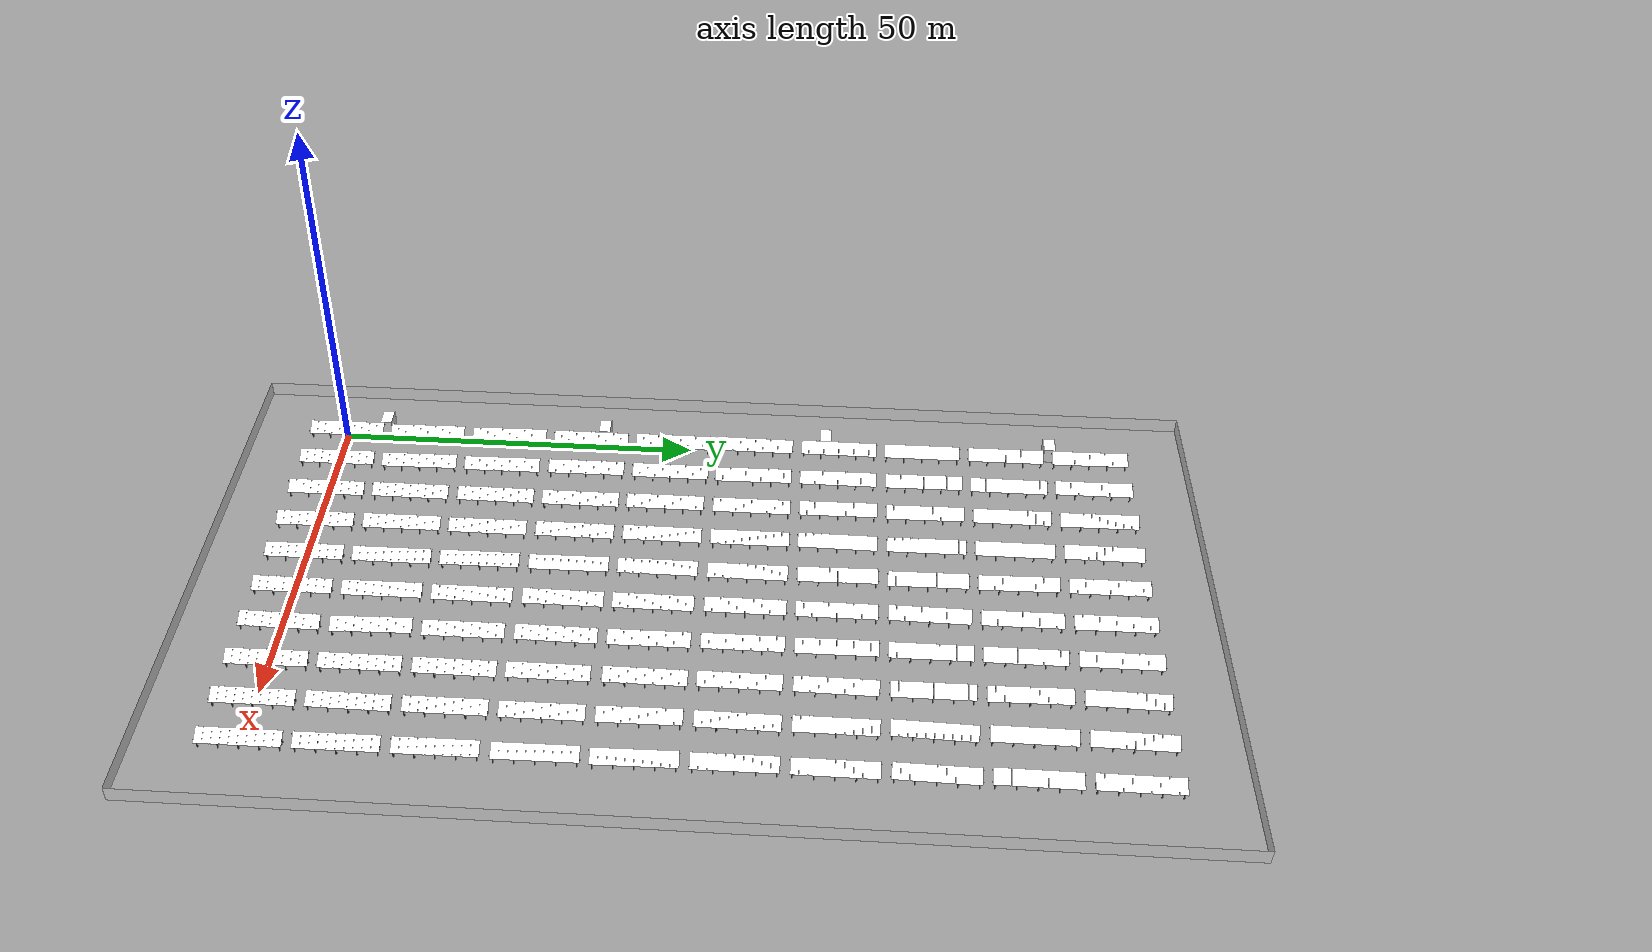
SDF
<sdf version="1.10">
 <world name="solar_farm">
  <physics name="default" type="ode">
   <max_step_size>0.001</max_step_size>
   <real_time_factor>1.0</real_time_factor>
  </physics>
  <plugin filename="gz-sim-physics-system" name="gz::sim::systems::Physics"/>
  <plugin filename="gz-sim-user-commands-system" name="gz::sim::systems::UserCommands"/>
  <plugin filename="gz-sim-scene-broadcaster-system" name="gz::sim::systems::SceneBroadcaster"/>
  <plugin filename="gz-sim-sensors-system" name="gz::sim::systems::Sensors">
   <render_engine>ogre2</render_engine>
  </plugin>
  <plugin filename="gz-sim-imu-system" name="gz::sim::systems::Imu"/>
  <plugin filename="gz-sim-navsat-system" name="gz::sim::systems::NavSat"/>
  <spherical_coordinates>
   <latitude_deg>-35.363262</latitude_deg>
   <longitude_deg>149.165237</longitude_deg>
   <elevation>584</elevation>
   <heading_deg>0</heading_deg>
   <surface_model>EARTH_WGS84</surface_model>
  </spherical_coordinates>
  <scene>
   <ambient>0.50 0.51 0.55 1</ambient>
   <background>0.62 0.72 0.85 1</background>
   <shadows>true</shadows>
   <grid>false</grid>
  </scene>
  <light type="directional" name="sun">
   <pose>0 0 60 0 0 0</pose>
   <diffuse>1.00 0.97 0.90 1</diffuse>
   <specular>0.35 0.35 0.33 1</specular>
   <direction>0.4394 -0.3687 -0.8192</direction>
   <attenuation>
    <range>1000</range>
    <constant>0.9</constant>
    <linear>0.0</linear>
    <quadratic>0.0</quadratic>
   </attenuation>
  </light>
  <model name="table_0000">
   <static>true</static>
   <pose>-0.004 0.024 0 0 0 0.00622</pose>
   <link name="table">
    <collision name="glass_col">
     <pose>0 0 1.6 0 0.488692 0</pose>
     <geometry><box><size>2.100 10.680 0.040</size></box></geometry>
    </collision>
    <visual name="glass">
     <pose>0 0 1.6 0 0.488692 0</pose>
     <geometry><mesh><uri>model://solar_farm_assets/meshes/pv_glass.obj</uri></mesh></geometry>
     <material>
      <ambient>0.25 0.25 0.25 1</ambient>
      <diffuse>1 1 1 1</diffuse>
      <specular>0.4 0.4 0.4 1</specular>
      <pbr>
       <metal>
        <albedo_map>model://solar_farm_assets/materials/textures/pv_atlas_07_albedo.png</albedo_map>
        <roughness_map>model://solar_farm_assets/materials/textures/pv_atlas_07_roughness.png</roughness_map>
        <normal_map>model://solar_farm_assets/materials/textures/pv_normal.png</normal_map>
        <metalness>0.1</metalness>
       </metal>
      </pbr>
     </material>
    </visual>
    <visual name="rack">
     <cast_shadows>false</cast_shadows>
     <geometry><mesh><uri>model://solar_farm_assets/meshes/pv_rack.obj</uri></mesh></geometry>
     <material>
      <ambient>0.18 0.18 0.20 1</ambient>
      <diffuse>0.40 0.41 0.43 1</diffuse>
      <specular>0.5 0.5 0.5 1</specular>
      <pbr><metal><roughness>0.45</roughness><metalness>0.85</metalness></metal></pbr>
     </material>
    </visual>
   </link>
  </model>
  <model name="table_0001">
   <static>true</static>
   <pose>0.085 11.881 0 0 0 0.01574</pose>
   <link name="table">
    <collision name="glass_col">
     <pose>0 0 1.6 0 0.488692 0</pose>
     <geometry><box><size>2.100 10.680 0.040</size></box></geometry>
    </collision>
    <visual name="glass">
     <pose>0 0 1.6 0 0.488692 0</pose>
     <geometry><mesh><uri>model://solar_farm_assets/meshes/pv_glass.obj</uri></mesh></geometry>
     <material>
      <ambient>0.25 0.25 0.25 1</ambient>
      <diffuse>1 1 1 1</diffuse>
      <specular>0.4 0.4 0.4 1</specular>
      <pbr>
       <metal>
        <albedo_map>model://solar_farm_assets/materials/textures/pv_atlas_05_albedo.png</albedo_map>
        <roughness_map>model://solar_farm_assets/materials/textures/pv_atlas_05_roughness.png</roughness_map>
        <normal_map>model://solar_farm_assets/materials/textures/pv_normal.png</normal_map>
        <metalness>0.1</metalness>
       </metal>
      </pbr>
     </material>
    </visual>
    <visual name="rack">
     <cast_shadows>false</cast_shadows>
     <geometry><mesh><uri>model://solar_farm_assets/meshes/pv_rack.obj</uri></mesh></geometry>
     <material>
      <ambient>0.18 0.18 0.20 1</ambient>
      <diffuse>0.40 0.41 0.43 1</diffuse>
      <specular>0.5 0.5 0.5 1</specular>
      <pbr><metal><roughness>0.45</roughness><metalness>0.85</metalness></metal></pbr>
     </material>
    </visual>
   </link>
  </model>
  <model name="table_0002">
   <static>true</static>
   <pose>0.010 23.819 0 0 0 0.01479</pose>
   <link name="table">
    <collision name="glass_col">
     <pose>0 0 1.6 0 0.488692 0</pose>
     <geometry><box><size>2.100 10.680 0.040</size></box></geometry>
    </collision>
    <visual name="glass">
     <pose>0 0 1.6 0 0.488692 0</pose>
     <geometry><mesh><uri>model://solar_farm_assets/meshes/pv_glass.obj</uri></mesh></geometry>
     <material>
      <ambient>0.25 0.25 0.25 1</ambient>
      <diffuse>1 1 1 1</diffuse>
      <specular>0.4 0.4 0.4 1</specular>
      <pbr>
       <metal>
        <albedo_map>model://solar_farm_assets/materials/textures/pv_atlas_14_albedo.png</albedo_map>
        <roughness_map>model://solar_farm_assets/materials/textures/pv_atlas_14_roughness.png</roughness_map>
        <normal_map>model://solar_farm_assets/materials/textures/pv_normal.png</normal_map>
        <metalness>0.1</metalness>
       </metal>
      </pbr>
     </material>
    </visual>
    <visual name="rack">
     <cast_shadows>false</cast_shadows>
     <geometry><mesh><uri>model://solar_farm_assets/meshes/pv_rack.obj</uri></mesh></geometry>
     <material>
      <ambient>0.18 0.18 0.20 1</ambient>
      <diffuse>0.40 0.41 0.43 1</diffuse>
      <specular>0.5 0.5 0.5 1</specular>
      <pbr><metal><roughness>0.45</roughness><metalness>0.85</metalness></metal></pbr>
     </material>
    </visual>
   </link>
  </model>
  <model name="table_0003">
   <static>true</static>
   <pose>0.030 35.671 0 0 0 -0.00415</pose>
   <link name="table">
    <collision name="glass_col">
     <pose>0 0 1.6 0 0.488692 0</pose>
     <geometry><box><size>2.100 10.680 0.040</size></box></geometry>
    </collision>
    <visual name="glass">
     <pose>0 0 1.6 0 0.488692 0</pose>
     <geometry><mesh><uri>model://solar_farm_assets/meshes/pv_glass.obj</uri></mesh></geometry>
     <material>
      <ambient>0.25 0.25 0.25 1</ambient>
      <diffuse>1 1 1 1</diffuse>
      <specular>0.4 0.4 0.4 1</specular>
      <pbr>
       <metal>
        <albedo_map>model://solar_farm_assets/materials/textures/pv_atlas_17_albedo.png</albedo_map>
        <roughness_map>model://solar_farm_assets/materials/textures/pv_atlas_17_roughness.png</roughness_map>
        <normal_map>model://solar_farm_assets/materials/textures/pv_normal.png</normal_map>
        <metalness>0.1</metalness>
       </metal>
      </pbr>
     </material>
    </visual>
    <visual name="rack">
     <cast_shadows>false</cast_shadows>
     <geometry><mesh><uri>model://solar_farm_assets/meshes/pv_rack.obj</uri></mesh></geometry>
     <material>
      <ambient>0.18 0.18 0.20 1</ambient>
      <diffuse>0.40 0.41 0.43 1</diffuse>
      <specular>0.5 0.5 0.5 1</specular>
      <pbr><metal><roughness>0.45</roughness><metalness>0.85</metalness></metal></pbr>
     </material>
    </visual>
   </link>
  </model>
  <model name="table_0004">
   <static>true</static>
   <pose>-0.028 47.537 0 0 0 -0.00335</pose>
   <link name="table">
    <collision name="glass_col">
     <pose>0 0 1.6 0 0.488692 0</pose>
     <geometry><box><size>2.100 10.680 0.040</size></box></geometry>
    </collision>
    <visual name="glass">
     <pose>0 0 1.6 0 0.488692 0</pose>
     <geometry><mesh><uri>model://solar_farm_assets/meshes/pv_glass.obj</uri></mesh></geometry>
     <material>
      <ambient>0.25 0.25 0.25 1</ambient>
      <diffuse>1 1 1 1</diffuse>
      <specular>0.4 0.4 0.4 1</specular>
      <pbr>
       <metal>
        <albedo_map>model://solar_farm_assets/materials/textures/pv_atlas_18_albedo.png</albedo_map>
        <roughness_map>model://solar_farm_assets/materials/textures/pv_atlas_18_roughness.png</roughness_map>
        <normal_map>model://solar_farm_assets/materials/textures/pv_normal.png</normal_map>
        <metalness>0.1</metalness>
       </metal>
      </pbr>
     </material>
    </visual>
    <visual name="rack">
     <cast_shadows>false</cast_shadows>
     <geometry><mesh><uri>model://solar_farm_assets/meshes/pv_rack.obj</uri></mesh></geometry>
     <material>
      <ambient>0.18 0.18 0.20 1</ambient>
      <diffuse>0.40 0.41 0.43 1</diffuse>
      <specular>0.5 0.5 0.5 1</specular>
      <pbr><metal><roughness>0.45</roughness><metalness>0.85</metalness></metal></pbr>
     </material>
    </visual>
   </link>
  </model>
  <model name="table_0005">
   <static>true</static>
   <pose>-0.051 59.386 0 0 0 -0.01309</pose>
   <link name="table">
    <collision name="glass_col">
     <pose>0 0 1.6 0 0.488692 0</pose>
     <geometry><box><size>2.100 10.680 0.040</size></box></geometry>
    </collision>
    <visual name="glass">
     <pose>0 0 1.6 0 0.488692 0</pose>
     <geometry><mesh><uri>model://solar_farm_assets/meshes/pv_glass.obj</uri></mesh></geometry>
     <material>
      <ambient>0.25 0.25 0.25 1</ambient>
      <diffuse>1 1 1 1</diffuse>
      <specular>0.4 0.4 0.4 1</specular>
      <pbr>
       <metal>
        <albedo_map>model://solar_farm_assets/materials/textures/pv_atlas_03_albedo.png</albedo_map>
        <roughness_map>model://solar_farm_assets/materials/textures/pv_atlas_03_roughness.png</roughness_map>
        <normal_map>model://solar_farm_assets/materials/textures/pv_normal.png</normal_map>
        <metalness>0.1</metalness>
       </metal>
      </pbr>
     </material>
    </visual>
    <visual name="rack">
     <cast_shadows>false</cast_shadows>
     <geometry><mesh><uri>model://solar_farm_assets/meshes/pv_rack.obj</uri></mesh></geometry>
     <material>
      <ambient>0.18 0.18 0.20 1</ambient>
      <diffuse>0.40 0.41 0.43 1</diffuse>
      <specular>0.5 0.5 0.5 1</specular>
      <pbr><metal><roughness>0.45</roughness><metalness>0.85</metalness></metal></pbr>
     </material>
    </visual>
   </link>
  </model>
  <model name="table_0006">
   <static>true</static>
   <pose>-0.049 71.330 0 0 0 -0.00557</pose>
   <link name="table">
    <collision name="glass_col">
     <pose>0 0 1.6 0 0.488692 0</pose>
     <geometry><box><size>2.100 10.680 0.040</size></box></geometry>
    </collision>
    <visual name="glass">
     <pose>0 0 1.6 0 0.488692 0</pose>
     <geometry><mesh><uri>model://solar_farm_assets/meshes/pv_glass.obj</uri></mesh></geometry>
     <material>
      <ambient>0.25 0.25 0.25 1</ambient>
      <diffuse>1 1 1 1</diffuse>
      <specular>0.4 0.4 0.4 1</specular>
      <pbr>
       <metal>
        <albedo_map>model://solar_farm_assets/materials/textures/pv_atlas_04_albedo.png</albedo_map>
        <roughness_map>model://solar_farm_assets/materials/textures/pv_atlas_04_roughness.png</roughness_map>
        <normal_map>model://solar_farm_assets/materials/textures/pv_normal.png</normal_map>
        <metalness>0.1</metalness>
       </metal>
      </pbr>
     </material>
    </visual>
    <visual name="rack">
     <cast_shadows>false</cast_shadows>
     <geometry><mesh><uri>model://solar_farm_assets/meshes/pv_rack.obj</uri></mesh></geometry>
     <material>
      <ambient>0.18 0.18 0.20 1</ambient>
      <diffuse>0.40 0.41 0.43 1</diffuse>
      <specular>0.5 0.5 0.5 1</specular>
      <pbr><metal><roughness>0.45</roughness><metalness>0.85</metalness></metal></pbr>
     </material>
    </visual>
   </link>
  </model>
  <model name="table_0007">
   <static>true</static>
   <pose>-0.022 83.192 0 0 0 0.00090</pose>
   <link name="table">
    <collision name="glass_col">
     <pose>0 0 1.6 0 0.488692 0</pose>
     <geometry><box><size>2.100 10.680 0.040</size></box></geometry>
    </collision>
    <visual name="glass">
     <pose>0 0 1.6 0 0.488692 0</pose>
     <geometry><mesh><uri>model://solar_farm_assets/meshes/pv_glass.obj</uri></mesh></geometry>
     <material>
      <ambient>0.25 0.25 0.25 1</ambient>
      <diffuse>1 1 1 1</diffuse>
      <specular>0.4 0.4 0.4 1</specular>
      <pbr>
       <metal>
        <albedo_map>model://solar_farm_assets/materials/textures/pv_atlas_00_albedo.png</albedo_map>
        <roughness_map>model://solar_farm_assets/materials/textures/pv_atlas_00_roughness.png</roughness_map>
        <normal_map>model://solar_farm_assets/materials/textures/pv_normal.png</normal_map>
        <metalness>0.1</metalness>
       </metal>
      </pbr>
     </material>
    </visual>
    <visual name="rack">
     <cast_shadows>false</cast_shadows>
     <geometry><mesh><uri>model://solar_farm_assets/meshes/pv_rack.obj</uri></mesh></geometry>
     <material>
      <ambient>0.18 0.18 0.20 1</ambient>
      <diffuse>0.40 0.41 0.43 1</diffuse>
      <specular>0.5 0.5 0.5 1</specular>
      <pbr><metal><roughness>0.45</roughness><metalness>0.85</metalness></metal></pbr>
     </material>
    </visual>
   </link>
  </model>
  <model name="table_0008">
   <static>true</static>
   <pose>-0.014 95.056 0 0 0 0.00251</pose>
   <link name="table">
    <collision name="glass_col">
     <pose>0 0 1.6 0 0.488692 0</pose>
     <geometry><box><size>2.100 10.680 0.040</size></box></geometry>
    </collision>
    <visual name="glass">
     <pose>0 0 1.6 0 0.488692 0</pose>
     <geometry><mesh><uri>model://solar_farm_assets/meshes/pv_glass.obj</uri></mesh></geometry>
     <material>
      <ambient>0.25 0.25 0.25 1</ambient>
      <diffuse>1 1 1 1</diffuse>
      <specular>0.4 0.4 0.4 1</specular>
      <pbr>
       <metal>
        <albedo_map>model://solar_farm_assets/materials/textures/pv_atlas_09_albedo.png</albedo_map>
        <roughness_map>model://solar_farm_assets/materials/textures/pv_atlas_09_roughness.png</roughness_map>
        <normal_map>model://solar_farm_assets/materials/textures/pv_normal.png</normal_map>
        <metalness>0.1</metalness>
       </metal>
      </pbr>
     </material>
    </visual>
    <visual name="rack">
     <cast_shadows>false</cast_shadows>
     <geometry><mesh><uri>model://solar_farm_assets/meshes/pv_rack.obj</uri></mesh></geometry>
     <material>
      <ambient>0.18 0.18 0.20 1</ambient>
      <diffuse>0.40 0.41 0.43 1</diffuse>
      <specular>0.5 0.5 0.5 1</specular>
      <pbr><metal><roughness>0.45</roughness><metalness>0.85</metalness></metal></pbr>
     </material>
    </visual>
   </link>
  </model>
  <model name="table_0009">
   <static>true</static>
   <pose>-0.078 106.938 0 0 0 0.01003</pose>
   <link name="table">
    <collision name="glass_col">
     <pose>0 0 1.6 0 0.488692 0</pose>
     <geometry><box><size>2.100 10.680 0.040</size></box></geometry>
    </collision>
    <visual name="glass">
     <pose>0 0 1.6 0 0.488692 0</pose>
     <geometry><mesh><uri>model://solar_farm_assets/meshes/pv_glass.obj</uri></mesh></geometry>
     <material>
      <ambient>0.25 0.25 0.25 1</ambient>
      <diffuse>1 1 1 1</diffuse>
      <specular>0.4 0.4 0.4 1</specular>
      <pbr>
       <metal>
        <albedo_map>model://solar_farm_assets/materials/textures/pv_atlas_10_albedo.png</albedo_map>
        <roughness_map>model://solar_farm_assets/materials/textures/pv_atlas_10_roughness.png</roughness_map>
        <normal_map>model://solar_farm_assets/materials/textures/pv_normal.png</normal_map>
        <metalness>0.1</metalness>
       </metal>
      </pbr>
     </material>
    </visual>
    <visual name="rack">
     <cast_shadows>false</cast_shadows>
     <geometry><mesh><uri>model://solar_farm_assets/meshes/pv_rack.obj</uri></mesh></geometry>
     <material>
      <ambient>0.18 0.18 0.20 1</ambient>
      <diffuse>0.40 0.41 0.43 1</diffuse>
      <specular>0.5 0.5 0.5 1</specular>
      <pbr><metal><roughness>0.45</roughness><metalness>0.85</metalness></metal></pbr>
     </material>
    </visual>
   </link>
  </model>
  <model name="table_0010">
   <static>true</static>
   <pose>6.442 0.004 0 0 0 0.00386</pose>
   <link name="table">
    <collision name="glass_col">
     <pose>0 0 1.6 0 0.488692 0</pose>
     <geometry><box><size>2.100 10.680 0.040</size></box></geometry>
    </collision>
    <visual name="glass">
     <pose>0 0 1.6 0 0.488692 0</pose>
     <geometry><mesh><uri>model://solar_farm_assets/meshes/pv_glass.obj</uri></mesh></geometry>
     <material>
      <ambient>0.25 0.25 0.25 1</ambient>
      <diffuse>1 1 1 1</diffuse>
      <specular>0.4 0.4 0.4 1</specular>
      <pbr>
       <metal>
        <albedo_map>model://solar_farm_assets/materials/textures/pv_atlas_06_albedo.png</albedo_map>
        <roughness_map>model://solar_farm_assets/materials/textures/pv_atlas_06_roughness.png</roughness_map>
        <normal_map>model://solar_farm_assets/materials/textures/pv_normal.png</normal_map>
        <metalness>0.1</metalness>
       </metal>
      </pbr>
     </material>
    </visual>
    <visual name="rack">
     <cast_shadows>false</cast_shadows>
     <geometry><mesh><uri>model://solar_farm_assets/meshes/pv_rack.obj</uri></mesh></geometry>
     <material>
      <ambient>0.18 0.18 0.20 1</ambient>
      <diffuse>0.40 0.41 0.43 1</diffuse>
      <specular>0.5 0.5 0.5 1</specular>
      <pbr><metal><roughness>0.45</roughness><metalness>0.85</metalness></metal></pbr>
     </material>
    </visual>
   </link>
  </model>
  <model name="table_0011">
   <static>true</static>
   <pose>6.492 11.845 0 0 0 0.01115</pose>
   <link name="table">
    <collision name="glass_col">
     <pose>0 0 1.6 0 0.488692 0</pose>
     <geometry><box><size>2.100 10.680 0.040</size></box></geometry>
    </collision>
    <visual name="glass">
     <pose>0 0 1.6 0 0.488692 0</pose>
     <geometry><mesh><uri>model://solar_farm_assets/meshes/pv_glass.obj</uri></mesh></geometry>
     <material>
      <ambient>0.25 0.25 0.25 1</ambient>
      <diffuse>1 1 1 1</diffuse>
      <specular>0.4 0.4 0.4 1</specular>
      <pbr>
       <metal>
        <albedo_map>model://solar_farm_assets/materials/textures/pv_atlas_11_albedo.png</albedo_map>
        <roughness_map>model://solar_farm_assets/materials/textures/pv_atlas_11_roughness.png</roughness_map>
        <normal_map>model://solar_farm_assets/materials/textures/pv_normal.png</normal_map>
        <metalness>0.1</metalness>
       </metal>
      </pbr>
     </material>
    </visual>
    <visual name="rack">
     <cast_shadows>false</cast_shadows>
     <geometry><mesh><uri>model://solar_farm_assets/meshes/pv_rack.obj</uri></mesh></geometry>
     <material>
      <ambient>0.18 0.18 0.20 1</ambient>
      <diffuse>0.40 0.41 0.43 1</diffuse>
      <specular>0.5 0.5 0.5 1</specular>
      <pbr><metal><roughness>0.45</roughness><metalness>0.85</metalness></metal></pbr>
     </material>
    </visual>
   </link>
  </model>
  <model name="table_0012">
   <static>true</static>
   <pose>6.516 23.714 0 0 0 0.00940</pose>
   <link name="table">
    <collision name="glass_col">
     <pose>0 0 1.6 0 0.488692 0</pose>
     <geometry><box><size>2.100 10.680 0.040</size></box></geometry>
    </collision>
    <visual name="glass">
     <pose>0 0 1.6 0 0.488692 0</pose>
     <geometry><mesh><uri>model://solar_farm_assets/meshes/pv_glass.obj</uri></mesh></geometry>
     <material>
      <ambient>0.25 0.25 0.25 1</ambient>
      <diffuse>1 1 1 1</diffuse>
      <specular>0.4 0.4 0.4 1</specular>
      <pbr>
       <metal>
        <albedo_map>model://solar_farm_assets/materials/textures/pv_atlas_12_albedo.png</albedo_map>
        <roughness_map>model://solar_farm_assets/materials/textures/pv_atlas_12_roughness.png</roughness_map>
        <normal_map>model://solar_farm_assets/materials/textures/pv_normal.png</normal_map>
        <metalness>0.1</metalness>
       </metal>
      </pbr>
     </material>
    </visual>
    <visual name="rack">
     <cast_shadows>false</cast_shadows>
     <geometry><mesh><uri>model://solar_farm_assets/meshes/pv_rack.obj</uri></mesh></geometry>
     <material>
      <ambient>0.18 0.18 0.20 1</ambient>
      <diffuse>0.40 0.41 0.43 1</diffuse>
      <specular>0.5 0.5 0.5 1</specular>
      <pbr><metal><roughness>0.45</roughness><metalness>0.85</metalness></metal></pbr>
     </material>
    </visual>
   </link>
  </model>
  <model name="table_0013">
   <static>true</static>
   <pose>6.402 35.710 0 0 0 0.01118</pose>
   <link name="table">
    <collision name="glass_col">
     <pose>0 0 1.6 0 0.488692 0</pose>
     <geometry><box><size>2.100 10.680 0.040</size></box></geometry>
    </collision>
    <visual name="glass">
     <pose>0 0 1.6 0 0.488692 0</pose>
     <geometry><mesh><uri>model://solar_farm_assets/meshes/pv_glass.obj</uri></mesh></geometry>
     <material>
      <ambient>0.25 0.25 0.25 1</ambient>
      <diffuse>1 1 1 1</diffuse>
      <specular>0.4 0.4 0.4 1</specular>
      <pbr>
       <metal>
        <albedo_map>model://solar_farm_assets/materials/textures/pv_atlas_16_albedo.png</albedo_map>
        <roughness_map>model://solar_farm_assets/materials/textures/pv_atlas_16_roughness.png</roughness_map>
        <normal_map>model://solar_farm_assets/materials/textures/pv_normal.png</normal_map>
        <metalness>0.1</metalness>
       </metal>
      </pbr>
     </material>
    </visual>
    <visual name="rack">
     <cast_shadows>false</cast_shadows>
     <geometry><mesh><uri>model://solar_farm_assets/meshes/pv_rack.obj</uri></mesh></geometry>
     <material>
      <ambient>0.18 0.18 0.20 1</ambient>
      <diffuse>0.40 0.41 0.43 1</diffuse>
      <specular>0.5 0.5 0.5 1</specular>
      <pbr><metal><roughness>0.45</roughness><metalness>0.85</metalness></metal></pbr>
     </material>
    </visual>
   </link>
  </model>
  <model name="table_0014">
   <static>true</static>
   <pose>6.471 47.633 0 0 0 -0.00559</pose>
   <link name="table">
    <collision name="glass_col">
     <pose>0 0 1.6 0 0.488692 0</pose>
     <geometry><box><size>2.100 10.680 0.040</size></box></geometry>
    </collision>
    <visual name="glass">
     <pose>0 0 1.6 0 0.488692 0</pose>
     <geometry><mesh><uri>model://solar_farm_assets/meshes/pv_glass.obj</uri></mesh></geometry>
     <material>
      <ambient>0.25 0.25 0.25 1</ambient>
      <diffuse>1 1 1 1</diffuse>
      <specular>0.4 0.4 0.4 1</specular>
      <pbr>
       <metal>
        <albedo_map>model://solar_farm_assets/materials/textures/pv_atlas_08_albedo.png</albedo_map>
        <roughness_map>model://solar_farm_assets/materials/textures/pv_atlas_08_roughness.png</roughness_map>
        <normal_map>model://solar_farm_assets/materials/textures/pv_normal.png</normal_map>
        <metalness>0.1</metalness>
       </metal>
      </pbr>
     </material>
    </visual>
    <visual name="rack">
     <cast_shadows>false</cast_shadows>
     <geometry><mesh><uri>model://solar_farm_assets/meshes/pv_rack.obj</uri></mesh></geometry>
     <material>
      <ambient>0.18 0.18 0.20 1</ambient>
      <diffuse>0.40 0.41 0.43 1</diffuse>
      <specular>0.5 0.5 0.5 1</specular>
      <pbr><metal><roughness>0.45</roughness><metalness>0.85</metalness></metal></pbr>
     </material>
    </visual>
   </link>
  </model>
  <model name="table_0015">
   <static>true</static>
   <pose>6.536 59.358 0 0 0 0.01509</pose>
   <link name="table">
    <collision name="glass_col">
     <pose>0 0 1.6 0 0.488692 0</pose>
     <geometry><box><size>2.100 10.680 0.040</size></box></geometry>
    </collision>
    <visual name="glass">
     <pose>0 0 1.6 0 0.488692 0</pose>
     <geometry><mesh><uri>model://solar_farm_assets/meshes/pv_glass.obj</uri></mesh></geometry>
     <material>
      <ambient>0.25 0.25 0.25 1</ambient>
      <diffuse>1 1 1 1</diffuse>
      <specular>0.4 0.4 0.4 1</specular>
      <pbr>
       <metal>
        <albedo_map>model://solar_farm_assets/materials/textures/pv_atlas_01_albedo.png</albedo_map>
        <roughness_map>model://solar_farm_assets/materials/textures/pv_atlas_01_roughness.png</roughness_map>
        <normal_map>model://solar_farm_assets/materials/textures/pv_normal.png</normal_map>
        <metalness>0.1</metalness>
       </metal>
      </pbr>
     </material>
    </visual>
    <visual name="rack">
     <cast_shadows>false</cast_shadows>
     <geometry><mesh><uri>model://solar_farm_assets/meshes/pv_rack.obj</uri></mesh></geometry>
     <material>
      <ambient>0.18 0.18 0.20 1</ambient>
      <diffuse>0.40 0.41 0.43 1</diffuse>
      <specular>0.5 0.5 0.5 1</specular>
      <pbr><metal><roughness>0.45</roughness><metalness>0.85</metalness></metal></pbr>
     </material>
    </visual>
   </link>
  </model>
  <model name="table_0016">
   <static>true</static>
   <pose>6.483 71.230 0 0 0 0.00044</pose>
   <link name="table">
    <collision name="glass_col">
     <pose>0 0 1.6 0 0.488692 0</pose>
     <geometry><box><size>2.100 10.680 0.040</size></box></geometry>
    </collision>
    <visual name="glass">
     <pose>0 0 1.6 0 0.488692 0</pose>
     <geometry><mesh><uri>model://solar_farm_assets/meshes/pv_glass.obj</uri></mesh></geometry>
     <material>
      <ambient>0.25 0.25 0.25 1</ambient>
      <diffuse>1 1 1 1</diffuse>
      <specular>0.4 0.4 0.4 1</specular>
      <pbr>
       <metal>
        <albedo_map>model://solar_farm_assets/materials/textures/pv_atlas_13_albedo.png</albedo_map>
        <roughness_map>model://solar_farm_assets/materials/textures/pv_atlas_13_roughness.png</roughness_map>
        <normal_map>model://solar_farm_assets/materials/textures/pv_normal.png</normal_map>
        <metalness>0.1</metalness>
       </metal>
      </pbr>
     </material>
    </visual>
    <visual name="rack">
     <cast_shadows>false</cast_shadows>
     <geometry><mesh><uri>model://solar_farm_assets/meshes/pv_rack.obj</uri></mesh></geometry>
     <material>
      <ambient>0.18 0.18 0.20 1</ambient>
      <diffuse>0.40 0.41 0.43 1</diffuse>
      <specular>0.5 0.5 0.5 1</specular>
      <pbr><metal><roughness>0.45</roughness><metalness>0.85</metalness></metal></pbr>
     </material>
    </visual>
   </link>
  </model>
  <model name="table_0017">
   <static>true</static>
   <pose>6.461 83.219 0 0 0 0.01231</pose>
   <link name="table">
    <collision name="glass_col">
     <pose>0 0 1.6 0 0.488692 0</pose>
     <geometry><box><size>2.100 10.680 0.040</size></box></geometry>
    </collision>
    <visual name="glass">
     <pose>0 0 1.6 0 0.488692 0</pose>
     <geometry><mesh><uri>model://solar_farm_assets/meshes/pv_glass.obj</uri></mesh></geometry>
     <material>
      <ambient>0.25 0.25 0.25 1</ambient>
      <diffuse>1 1 1 1</diffuse>
      <specular>0.4 0.4 0.4 1</specular>
      <pbr>
       <metal>
        <albedo_map>model://solar_farm_assets/materials/textures/pv_atlas_02_albedo.png</albedo_map>
        <roughness_map>model://solar_farm_assets/materials/textures/pv_atlas_02_roughness.png</roughness_map>
        <normal_map>model://solar_farm_assets/materials/textures/pv_normal.png</normal_map>
        <metalness>0.1</metalness>
       </metal>
      </pbr>
     </material>
    </visual>
    <visual name="rack">
     <cast_shadows>false</cast_shadows>
     <geometry><mesh><uri>model://solar_farm_assets/meshes/pv_rack.obj</uri></mesh></geometry>
     <material>
      <ambient>0.18 0.18 0.20 1</ambient>
      <diffuse>0.40 0.41 0.43 1</diffuse>
      <specular>0.5 0.5 0.5 1</specular>
      <pbr><metal><roughness>0.45</roughness><metalness>0.85</metalness></metal></pbr>
     </material>
    </visual>
   </link>
  </model>
  <model name="table_0018">
   <static>true</static>
   <pose>6.539 95.059 0 0 0 -0.00374</pose>
   <link name="table">
    <collision name="glass_col">
     <pose>0 0 1.6 0 0.488692 0</pose>
     <geometry><box><size>2.100 10.680 0.040</size></box></geometry>
    </collision>
    <visual name="glass">
     <pose>0 0 1.6 0 0.488692 0</pose>
     <geometry><mesh><uri>model://solar_farm_assets/meshes/pv_glass.obj</uri></mesh></geometry>
     <material>
      <ambient>0.25 0.25 0.25 1</ambient>
      <diffuse>1 1 1 1</diffuse>
      <specular>0.4 0.4 0.4 1</specular>
      <pbr>
       <metal>
        <albedo_map>model://solar_farm_assets/materials/textures/pv_atlas_19_albedo.png</albedo_map>
        <roughness_map>model://solar_farm_assets/materials/textures/pv_atlas_19_roughness.png</roughness_map>
        <normal_map>model://solar_farm_assets/materials/textures/pv_normal.png</normal_map>
        <metalness>0.1</metalness>
       </metal>
      </pbr>
     </material>
    </visual>
    <visual name="rack">
     <cast_shadows>false</cast_shadows>
     <geometry><mesh><uri>model://solar_farm_assets/meshes/pv_rack.obj</uri></mesh></geometry>
     <material>
      <ambient>0.18 0.18 0.20 1</ambient>
      <diffuse>0.40 0.41 0.43 1</diffuse>
      <specular>0.5 0.5 0.5 1</specular>
      <pbr><metal><roughness>0.45</roughness><metalness>0.85</metalness></metal></pbr>
     </material>
    </visual>
   </link>
  </model>
  <model name="table_0019">
   <static>true</static>
   <pose>6.405 106.849 0 0 0 0.00211</pose>
   <link name="table">
    <collision name="glass_col">
     <pose>0 0 1.6 0 0.488692 0</pose>
     <geometry><box><size>2.100 10.680 0.040</size></box></geometry>
    </collision>
    <visual name="glass">
     <pose>0 0 1.6 0 0.488692 0</pose>
     <geometry><mesh><uri>model://solar_farm_assets/meshes/pv_glass.obj</uri></mesh></geometry>
     <material>
      <ambient>0.25 0.25 0.25 1</ambient>
      <diffuse>1 1 1 1</diffuse>
      <specular>0.4 0.4 0.4 1</specular>
      <pbr>
       <metal>
        <albedo_map>model://solar_farm_assets/materials/textures/pv_atlas_15_albedo.png</albedo_map>
        <roughness_map>model://solar_farm_assets/materials/textures/pv_atlas_15_roughness.png</roughness_map>
        <normal_map>model://solar_farm_assets/materials/textures/pv_normal.png</normal_map>
        <metalness>0.1</metalness>
       </metal>
      </pbr>
     </material>
    </visual>
    <visual name="rack">
     <cast_shadows>false</cast_shadows>
     <geometry><mesh><uri>model://solar_farm_assets/meshes/pv_rack.obj</uri></mesh></geometry>
     <material>
      <ambient>0.18 0.18 0.20 1</ambient>
      <diffuse>0.40 0.41 0.43 1</diffuse>
      <specular>0.5 0.5 0.5 1</specular>
      <pbr><metal><roughness>0.45</roughness><metalness>0.85</metalness></metal></pbr>
     </material>
    </visual>
   </link>
  </model>
  <model name="table_0020">
   <static>true</static>
   <pose>13.037 -0.000 0 0 0 0.00254</pose>
   <link name="table">
    <collision name="glass_col">
     <pose>0 0 1.6 0 0.488692 0</pose>
     <geometry><box><size>2.100 10.680 0.040</size></box></geometry>
    </collision>
    <visual name="glass">
     <pose>0 0 1.6 0 0.488692 0</pose>
     <geometry><mesh><uri>model://solar_farm_assets/meshes/pv_glass.obj</uri></mesh></geometry>
     <material>
      <ambient>0.25 0.25 0.25 1</ambient>
      <diffuse>1 1 1 1</diffuse>
      <specular>0.4 0.4 0.4 1</specular>
      <pbr>
       <metal>
        <albedo_map>model://solar_farm_assets/materials/textures/pv_atlas_18_albedo.png</albedo_map>
        <roughness_map>model://solar_farm_assets/materials/textures/pv_atlas_18_roughness.png</roughness_map>
        <normal_map>model://solar_farm_assets/materials/textures/pv_normal.png</normal_map>
        <metalness>0.1</metalness>
       </metal>
      </pbr>
     </material>
    </visual>
    <visual name="rack">
     <cast_shadows>false</cast_shadows>
     <geometry><mesh><uri>model://solar_farm_assets/meshes/pv_rack.obj</uri></mesh></geometry>
     <material>
      <ambient>0.18 0.18 0.20 1</ambient>
      <diffuse>0.40 0.41 0.43 1</diffuse>
      <specular>0.5 0.5 0.5 1</specular>
      <pbr><metal><roughness>0.45</roughness><metalness>0.85</metalness></metal></pbr>
     </material>
    </visual>
   </link>
  </model>
  <model name="table_0021">
   <static>true</static>
   <pose>12.980 11.848 0 0 0 -0.00539</pose>
   <link name="table">
    <collision name="glass_col">
     <pose>0 0 1.6 0 0.488692 0</pose>
     <geometry><box><size>2.100 10.680 0.040</size></box></geometry>
    </collision>
    <visual name="glass">
     <pose>0 0 1.6 0 0.488692 0</pose>
     <geometry><mesh><uri>model://solar_farm_assets/meshes/pv_glass.obj</uri></mesh></geometry>
     <material>
      <ambient>0.25 0.25 0.25 1</ambient>
      <diffuse>1 1 1 1</diffuse>
      <specular>0.4 0.4 0.4 1</specular>
      <pbr>
       <metal>
        <albedo_map>model://solar_farm_assets/materials/textures/pv_atlas_04_albedo.png</albedo_map>
        <roughness_map>model://solar_farm_assets/materials/textures/pv_atlas_04_roughness.png</roughness_map>
        <normal_map>model://solar_farm_assets/materials/textures/pv_normal.png</normal_map>
        <metalness>0.1</metalness>
       </metal>
      </pbr>
     </material>
    </visual>
    <visual name="rack">
     <cast_shadows>false</cast_shadows>
     <geometry><mesh><uri>model://solar_farm_assets/meshes/pv_rack.obj</uri></mesh></geometry>
     <material>
      <ambient>0.18 0.18 0.20 1</ambient>
      <diffuse>0.40 0.41 0.43 1</diffuse>
      <specular>0.5 0.5 0.5 1</specular>
      <pbr><metal><roughness>0.45</roughness><metalness>0.85</metalness></metal></pbr>
     </material>
    </visual>
   </link>
  </model>
  <model name="table_0022">
   <static>true</static>
   <pose>13.007 23.825 0 0 0 -0.00514</pose>
   <link name="table">
    <collision name="glass_col">
     <pose>0 0 1.6 0 0.488692 0</pose>
     <geometry><box><size>2.100 10.680 0.040</size></box></geometry>
    </collision>
    <visual name="glass">
     <pose>0 0 1.6 0 0.488692 0</pose>
     <geometry><mesh><uri>model://solar_farm_assets/meshes/pv_glass.obj</uri></mesh></geometry>
     <material>
      <ambient>0.25 0.25 0.25 1</ambient>
      <diffuse>1 1 1 1</diffuse>
      <specular>0.4 0.4 0.4 1</specular>
      <pbr>
       <metal>
        <albedo_map>model://solar_farm_assets/materials/textures/pv_atlas_08_albedo.png</albedo_map>
        <roughness_map>model://solar_farm_assets/materials/textures/pv_atlas_08_roughness.png</roughness_map>
        <normal_map>model://solar_farm_assets/materials/textures/pv_normal.png</normal_map>
        <metalness>0.1</metalness>
       </metal>
      </pbr>
     </material>
    </visual>
    <visual name="rack">
     <cast_shadows>false</cast_shadows>
     <geometry><mesh><uri>model://solar_farm_assets/meshes/pv_rack.obj</uri></mesh></geometry>
     <material>
      <ambient>0.18 0.18 0.20 1</ambient>
      <diffuse>0.40 0.41 0.43 1</diffuse>
      <specular>0.5 0.5 0.5 1</specular>
      <pbr><metal><roughness>0.45</roughness><metalness>0.85</metalness></metal></pbr>
     </material>
    </visual>
   </link>
  </model>
  <model name="table_0023">
   <static>true</static>
   <pose>13.054 35.661 0 0 0 0.00059</pose>
   <link name="table">
    <collision name="glass_col">
     <pose>0 0 1.6 0 0.488692 0</pose>
     <geometry><box><size>2.100 10.680 0.040</size></box></geometry>
    </collision>
    <visual name="glass">
     <pose>0 0 1.6 0 0.488692 0</pose>
     <geometry><mesh><uri>model://solar_farm_assets/meshes/pv_glass.obj</uri></mesh></geometry>
     <material>
      <ambient>0.25 0.25 0.25 1</ambient>
      <diffuse>1 1 1 1</diffuse>
      <specular>0.4 0.4 0.4 1</specular>
      <pbr>
       <metal>
        <albedo_map>model://solar_farm_assets/materials/textures/pv_atlas_15_albedo.png</albedo_map>
        <roughness_map>model://solar_farm_assets/materials/textures/pv_atlas_15_roughness.png</roughness_map>
        <normal_map>model://solar_farm_assets/materials/textures/pv_normal.png</normal_map>
        <metalness>0.1</metalness>
       </metal>
      </pbr>
     </material>
    </visual>
    <visual name="rack">
     <cast_shadows>false</cast_shadows>
     <geometry><mesh><uri>model://solar_farm_assets/meshes/pv_rack.obj</uri></mesh></geometry>
     <material>
      <ambient>0.18 0.18 0.20 1</ambient>
      <diffuse>0.40 0.41 0.43 1</diffuse>
      <specular>0.5 0.5 0.5 1</specular>
      <pbr><metal><roughness>0.45</roughness><metalness>0.85</metalness></metal></pbr>
     </material>
    </visual>
   </link>
  </model>
  <model name="table_0024">
   <static>true</static>
   <pose>12.987 47.448 0 0 0 -0.00189</pose>
   <link name="table">
    <collision name="glass_col">
     <pose>0 0 1.6 0 0.488692 0</pose>
     <geometry><box><size>2.100 10.680 0.040</size></box></geometry>
    </collision>
    <visual name="glass">
     <pose>0 0 1.6 0 0.488692 0</pose>
     <geometry><mesh><uri>model://solar_farm_assets/meshes/pv_glass.obj</uri></mesh></geometry>
     <material>
      <ambient>0.25 0.25 0.25 1</ambient>
      <diffuse>1 1 1 1</diffuse>
      <specular>0.4 0.4 0.4 1</specular>
      <pbr>
       <metal>
        <albedo_map>model://solar_farm_assets/materials/textures/pv_atlas_01_albedo.png</albedo_map>
        <roughness_map>model://solar_farm_assets/materials/textures/pv_atlas_01_roughness.png</roughness_map>
        <normal_map>model://solar_farm_assets/materials/textures/pv_normal.png</normal_map>
        <metalness>0.1</metalness>
       </metal>
      </pbr>
     </material>
    </visual>
    <visual name="rack">
     <cast_shadows>false</cast_shadows>
     <geometry><mesh><uri>model://solar_farm_assets/meshes/pv_rack.obj</uri></mesh></geometry>
     <material>
      <ambient>0.18 0.18 0.20 1</ambient>
      <diffuse>0.40 0.41 0.43 1</diffuse>
      <specular>0.5 0.5 0.5 1</specular>
      <pbr><metal><roughness>0.45</roughness><metalness>0.85</metalness></metal></pbr>
     </material>
    </visual>
   </link>
  </model>
  <model name="table_0025">
   <static>true</static>
   <pose>13.041 59.398 0 0 0 -0.00343</pose>
   <link name="table">
    <collision name="glass_col">
     <pose>0 0 1.6 0 0.488692 0</pose>
     <geometry><box><size>2.100 10.680 0.040</size></box></geometry>
    </collision>
    <visual name="glass">
     <pose>0 0 1.6 0 0.488692 0</pose>
     <geometry><mesh><uri>model://solar_farm_assets/meshes/pv_glass.obj</uri></mesh></geometry>
     <material>
      <ambient>0.25 0.25 0.25 1</ambient>
      <diffuse>1 1 1 1</diffuse>
      <specular>0.4 0.4 0.4 1</specular>
      <pbr>
       <metal>
        <albedo_map>model://solar_farm_assets/materials/textures/pv_atlas_06_albedo.png</albedo_map>
        <roughness_map>model://solar_farm_assets/materials/textures/pv_atlas_06_roughness.png</roughness_map>
        <normal_map>model://solar_farm_assets/materials/textures/pv_normal.png</normal_map>
        <metalness>0.1</metalness>
       </metal>
      </pbr>
     </material>
    </visual>
    <visual name="rack">
     <cast_shadows>false</cast_shadows>
     <geometry><mesh><uri>model://solar_farm_assets/meshes/pv_rack.obj</uri></mesh></geometry>
     <material>
      <ambient>0.18 0.18 0.20 1</ambient>
      <diffuse>0.40 0.41 0.43 1</diffuse>
      <specular>0.5 0.5 0.5 1</specular>
      <pbr><metal><roughness>0.45</roughness><metalness>0.85</metalness></metal></pbr>
     </material>
    </visual>
   </link>
  </model>
  <model name="table_0026">
   <static>true</static>
   <pose>12.920 71.297 0 0 0 0.01372</pose>
   <link name="table">
    <collision name="glass_col">
     <pose>0 0 1.6 0 0.488692 0</pose>
     <geometry><box><size>2.100 10.680 0.040</size></box></geometry>
    </collision>
    <visual name="glass">
     <pose>0 0 1.6 0 0.488692 0</pose>
     <geometry><mesh><uri>model://solar_farm_assets/meshes/pv_glass.obj</uri></mesh></geometry>
     <material>
      <ambient>0.25 0.25 0.25 1</ambient>
      <diffuse>1 1 1 1</diffuse>
      <specular>0.4 0.4 0.4 1</specular>
      <pbr>
       <metal>
        <albedo_map>model://solar_farm_assets/materials/textures/pv_atlas_10_albedo.png</albedo_map>
        <roughness_map>model://solar_farm_assets/materials/textures/pv_atlas_10_roughness.png</roughness_map>
        <normal_map>model://solar_farm_assets/materials/textures/pv_normal.png</normal_map>
        <metalness>0.1</metalness>
       </metal>
      </pbr>
     </material>
    </visual>
    <visual name="rack">
     <cast_shadows>false</cast_shadows>
     <geometry><mesh><uri>model://solar_farm_assets/meshes/pv_rack.obj</uri></mesh></geometry>
     <material>
      <ambient>0.18 0.18 0.20 1</ambient>
      <diffuse>0.40 0.41 0.43 1</diffuse>
      <specular>0.5 0.5 0.5 1</specular>
      <pbr><metal><roughness>0.45</roughness><metalness>0.85</metalness></metal></pbr>
     </material>
    </visual>
   </link>
  </model>
  <model name="table_0027">
   <static>true</static>
   <pose>12.981 83.192 0 0 0 0.01291</pose>
   <link name="table">
    <collision name="glass_col">
     <pose>0 0 1.6 0 0.488692 0</pose>
     <geometry><box><size>2.100 10.680 0.040</size></box></geometry>
    </collision>
    <visual name="glass">
     <pose>0 0 1.6 0 0.488692 0</pose>
     <geometry><mesh><uri>model://solar_farm_assets/meshes/pv_glass.obj</uri></mesh></geometry>
     <material>
      <ambient>0.25 0.25 0.25 1</ambient>
      <diffuse>1 1 1 1</diffuse>
      <specular>0.4 0.4 0.4 1</specular>
      <pbr>
       <metal>
        <albedo_map>model://solar_farm_assets/materials/textures/pv_atlas_19_albedo.png</albedo_map>
        <roughness_map>model://solar_farm_assets/materials/textures/pv_atlas_19_roughness.png</roughness_map>
        <normal_map>model://solar_farm_assets/materials/textures/pv_normal.png</normal_map>
        <metalness>0.1</metalness>
       </metal>
      </pbr>
     </material>
    </visual>
    <visual name="rack">
     <cast_shadows>false</cast_shadows>
     <geometry><mesh><uri>model://solar_farm_assets/meshes/pv_rack.obj</uri></mesh></geometry>
     <material>
      <ambient>0.18 0.18 0.20 1</ambient>
      <diffuse>0.40 0.41 0.43 1</diffuse>
      <specular>0.5 0.5 0.5 1</specular>
      <pbr><metal><roughness>0.45</roughness><metalness>0.85</metalness></metal></pbr>
     </material>
    </visual>
   </link>
  </model>
  <model name="table_0028">
   <static>true</static>
   <pose>12.994 95.047 0 0 0 0.00016</pose>
   <link name="table">
    <collision name="glass_col">
     <pose>0 0 1.6 0 0.488692 0</pose>
     <geometry><box><size>2.100 10.680 0.040</size></box></geometry>
    </collision>
    <visual name="glass">
     <pose>0 0 1.6 0 0.488692 0</pose>
     <geometry><mesh><uri>model://solar_farm_assets/meshes/pv_glass.obj</uri></mesh></geometry>
     <material>
      <ambient>0.25 0.25 0.25 1</ambient>
      <diffuse>1 1 1 1</diffuse>
      <specular>0.4 0.4 0.4 1</specular>
      <pbr>
       <metal>
        <albedo_map>model://solar_farm_assets/materials/textures/pv_atlas_13_albedo.png</albedo_map>
        <roughness_map>model://solar_farm_assets/materials/textures/pv_atlas_13_roughness.png</roughness_map>
        <normal_map>model://solar_farm_assets/materials/textures/pv_normal.png</normal_map>
        <metalness>0.1</metalness>
       </metal>
      </pbr>
     </material>
    </visual>
    <visual name="rack">
     <cast_shadows>false</cast_shadows>
     <geometry><mesh><uri>model://solar_farm_assets/meshes/pv_rack.obj</uri></mesh></geometry>
     <material>
      <ambient>0.18 0.18 0.20 1</ambient>
      <diffuse>0.40 0.41 0.43 1</diffuse>
      <specular>0.5 0.5 0.5 1</specular>
      <pbr><metal><roughness>0.45</roughness><metalness>0.85</metalness></metal></pbr>
     </material>
    </visual>
   </link>
  </model>
  <model name="table_0029">
   <static>true</static>
   <pose>13.030 106.926 0 0 0 0.00944</pose>
   <link name="table">
    <collision name="glass_col">
     <pose>0 0 1.6 0 0.488692 0</pose>
     <geometry><box><size>2.100 10.680 0.040</size></box></geometry>
    </collision>
    <visual name="glass">
     <pose>0 0 1.6 0 0.488692 0</pose>
     <geometry><mesh><uri>model://solar_farm_assets/meshes/pv_glass.obj</uri></mesh></geometry>
     <material>
      <ambient>0.25 0.25 0.25 1</ambient>
      <diffuse>1 1 1 1</diffuse>
      <specular>0.4 0.4 0.4 1</specular>
      <pbr>
       <metal>
        <albedo_map>model://solar_farm_assets/materials/textures/pv_atlas_03_albedo.png</albedo_map>
        <roughness_map>model://solar_farm_assets/materials/textures/pv_atlas_03_roughness.png</roughness_map>
        <normal_map>model://solar_farm_assets/materials/textures/pv_normal.png</normal_map>
        <metalness>0.1</metalness>
       </metal>
      </pbr>
     </material>
    </visual>
    <visual name="rack">
     <cast_shadows>false</cast_shadows>
     <geometry><mesh><uri>model://solar_farm_assets/meshes/pv_rack.obj</uri></mesh></geometry>
     <material>
      <ambient>0.18 0.18 0.20 1</ambient>
      <diffuse>0.40 0.41 0.43 1</diffuse>
      <specular>0.5 0.5 0.5 1</specular>
      <pbr><metal><roughness>0.45</roughness><metalness>0.85</metalness></metal></pbr>
     </material>
    </visual>
   </link>
  </model>
  <model name="table_0030">
   <static>true</static>
   <pose>19.559 -0.026 0 0 0 0.01106</pose>
   <link name="table">
    <collision name="glass_col">
     <pose>0 0 1.6 0 0.488692 0</pose>
     <geometry><box><size>2.100 10.680 0.040</size></box></geometry>
    </collision>
    <visual name="glass">
     <pose>0 0 1.6 0 0.488692 0</pose>
     <geometry><mesh><uri>model://solar_farm_assets/meshes/pv_glass.obj</uri></mesh></geometry>
     <material>
      <ambient>0.25 0.25 0.25 1</ambient>
      <diffuse>1 1 1 1</diffuse>
      <specular>0.4 0.4 0.4 1</specular>
      <pbr>
       <metal>
        <albedo_map>model://solar_farm_assets/materials/textures/pv_atlas_00_albedo.png</albedo_map>
        <roughness_map>model://solar_farm_assets/materials/textures/pv_atlas_00_roughness.png</roughness_map>
        <normal_map>model://solar_farm_assets/materials/textures/pv_normal.png</normal_map>
        <metalness>0.1</metalness>
       </metal>
      </pbr>
     </material>
    </visual>
    <visual name="rack">
     <cast_shadows>false</cast_shadows>
     <geometry><mesh><uri>model://solar_farm_assets/meshes/pv_rack.obj</uri></mesh></geometry>
     <material>
      <ambient>0.18 0.18 0.20 1</ambient>
      <diffuse>0.40 0.41 0.43 1</diffuse>
      <specular>0.5 0.5 0.5 1</specular>
      <pbr><metal><roughness>0.45</roughness><metalness>0.85</metalness></metal></pbr>
     </material>
    </visual>
   </link>
  </model>
  <model name="table_0031">
   <static>true</static>
   <pose>19.452 11.926 0 0 0 -0.00054</pose>
   <link name="table">
    <collision name="glass_col">
     <pose>0 0 1.6 0 0.488692 0</pose>
     <geometry><box><size>2.100 10.680 0.040</size></box></geometry>
    </collision>
    <visual name="glass">
     <pose>0 0 1.6 0 0.488692 0</pose>
     <geometry><mesh><uri>model://solar_farm_assets/meshes/pv_glass.obj</uri></mesh></geometry>
     <material>
      <ambient>0.25 0.25 0.25 1</ambient>
      <diffuse>1 1 1 1</diffuse>
      <specular>0.4 0.4 0.4 1</specular>
      <pbr>
       <metal>
        <albedo_map>model://solar_farm_assets/materials/textures/pv_atlas_07_albedo.png</albedo_map>
        <roughness_map>model://solar_farm_assets/materials/textures/pv_atlas_07_roughness.png</roughness_map>
        <normal_map>model://solar_farm_assets/materials/textures/pv_normal.png</normal_map>
        <metalness>0.1</metalness>
       </metal>
      </pbr>
     </material>
    </visual>
    <visual name="rack">
     <cast_shadows>false</cast_shadows>
     <geometry><mesh><uri>model://solar_farm_assets/meshes/pv_rack.obj</uri></mesh></geometry>
     <material>
      <ambient>0.18 0.18 0.20 1</ambient>
      <diffuse>0.40 0.41 0.43 1</diffuse>
      <specular>0.5 0.5 0.5 1</specular>
      <pbr><metal><roughness>0.45</roughness><metalness>0.85</metalness></metal></pbr>
     </material>
    </visual>
   </link>
  </model>
  <model name="table_0032">
   <static>true</static>
   <pose>19.539 23.746 0 0 0 -0.00220</pose>
   <link name="table">
    <collision name="glass_col">
     <pose>0 0 1.6 0 0.488692 0</pose>
     <geometry><box><size>2.100 10.680 0.040</size></box></geometry>
    </collision>
    <visual name="glass">
     <pose>0 0 1.6 0 0.488692 0</pose>
     <geometry><mesh><uri>model://solar_farm_assets/meshes/pv_glass.obj</uri></mesh></geometry>
     <material>
      <ambient>0.25 0.25 0.25 1</ambient>
      <diffuse>1 1 1 1</diffuse>
      <specular>0.4 0.4 0.4 1</specular>
      <pbr>
       <metal>
        <albedo_map>model://solar_farm_assets/materials/textures/pv_atlas_05_albedo.png</albedo_map>
        <roughness_map>model://solar_farm_assets/materials/textures/pv_atlas_05_roughness.png</roughness_map>
        <normal_map>model://solar_farm_assets/materials/textures/pv_normal.png</normal_map>
        <metalness>0.1</metalness>
       </metal>
      </pbr>
     </material>
    </visual>
    <visual name="rack">
     <cast_shadows>false</cast_shadows>
     <geometry><mesh><uri>model://solar_farm_assets/meshes/pv_rack.obj</uri></mesh></geometry>
     <material>
      <ambient>0.18 0.18 0.20 1</ambient>
      <diffuse>0.40 0.41 0.43 1</diffuse>
      <specular>0.5 0.5 0.5 1</specular>
      <pbr><metal><roughness>0.45</roughness><metalness>0.85</metalness></metal></pbr>
     </material>
    </visual>
   </link>
  </model>
  <model name="table_0033">
   <static>true</static>
   <pose>19.518 35.666 0 0 0 -0.00690</pose>
   <link name="table">
    <collision name="glass_col">
     <pose>0 0 1.6 0 0.488692 0</pose>
     <geometry><box><size>2.100 10.680 0.040</size></box></geometry>
    </collision>
    <visual name="glass">
     <pose>0 0 1.6 0 0.488692 0</pose>
     <geometry><mesh><uri>model://solar_farm_assets/meshes/pv_glass.obj</uri></mesh></geometry>
     <material>
      <ambient>0.25 0.25 0.25 1</ambient>
      <diffuse>1 1 1 1</diffuse>
      <specular>0.4 0.4 0.4 1</specular>
      <pbr>
       <metal>
        <albedo_map>model://solar_farm_assets/materials/textures/pv_atlas_11_albedo.png</albedo_map>
        <roughness_map>model://solar_farm_assets/materials/textures/pv_atlas_11_roughness.png</roughness_map>
        <normal_map>model://solar_farm_assets/materials/textures/pv_normal.png</normal_map>
        <metalness>0.1</metalness>
       </metal>
      </pbr>
     </material>
    </visual>
    <visual name="rack">
     <cast_shadows>false</cast_shadows>
     <geometry><mesh><uri>model://solar_farm_assets/meshes/pv_rack.obj</uri></mesh></geometry>
     <material>
      <ambient>0.18 0.18 0.20 1</ambient>
      <diffuse>0.40 0.41 0.43 1</diffuse>
      <specular>0.5 0.5 0.5 1</specular>
      <pbr><metal><roughness>0.45</roughness><metalness>0.85</metalness></metal></pbr>
     </material>
    </visual>
   </link>
  </model>
  <model name="table_0034">
   <static>true</static>
   <pose>19.499 47.564 0 0 0 -0.00833</pose>
   <link name="table">
    <collision name="glass_col">
     <pose>0 0 1.6 0 0.488692 0</pose>
     <geometry><box><size>2.100 10.680 0.040</size></box></geometry>
    </collision>
    <visual name="glass">
     <pose>0 0 1.6 0 0.488692 0</pose>
     <geometry><mesh><uri>model://solar_farm_assets/meshes/pv_glass.obj</uri></mesh></geometry>
     <material>
      <ambient>0.25 0.25 0.25 1</ambient>
      <diffuse>1 1 1 1</diffuse>
      <specular>0.4 0.4 0.4 1</specular>
      <pbr>
       <metal>
        <albedo_map>model://solar_farm_assets/materials/textures/pv_atlas_17_albedo.png</albedo_map>
        <roughness_map>model://solar_farm_assets/materials/textures/pv_atlas_17_roughness.png</roughness_map>
        <normal_map>model://solar_farm_assets/materials/textures/pv_normal.png</normal_map>
        <metalness>0.1</metalness>
       </metal>
      </pbr>
     </material>
    </visual>
    <visual name="rack">
     <cast_shadows>false</cast_shadows>
     <geometry><mesh><uri>model://solar_farm_assets/meshes/pv_rack.obj</uri></mesh></geometry>
     <material>
      <ambient>0.18 0.18 0.20 1</ambient>
      <diffuse>0.40 0.41 0.43 1</diffuse>
      <specular>0.5 0.5 0.5 1</specular>
      <pbr><metal><roughness>0.45</roughness><metalness>0.85</metalness></metal></pbr>
     </material>
    </visual>
   </link>
  </model>
  <model name="table_0035">
   <static>true</static>
   <pose>19.528 59.456 0 0 0 0.00316</pose>
   <link name="table">
    <collision name="glass_col">
     <pose>0 0 1.6 0 0.488692 0</pose>
     <geometry><box><size>2.100 10.680 0.040</size></box></geometry>
    </collision>
    <visual name="glass">
     <pose>0 0 1.6 0 0.488692 0</pose>
     <geometry><mesh><uri>model://solar_farm_assets/meshes/pv_glass.obj</uri></mesh></geometry>
     <material>
      <ambient>0.25 0.25 0.25 1</ambient>
      <diffuse>1 1 1 1</diffuse>
      <specular>0.4 0.4 0.4 1</specular>
      <pbr>
       <metal>
        <albedo_map>model://solar_farm_assets/materials/textures/pv_atlas_14_albedo.png</albedo_map>
        <roughness_map>model://solar_farm_assets/materials/textures/pv_atlas_14_roughness.png</roughness_map>
        <normal_map>model://solar_farm_assets/materials/textures/pv_normal.png</normal_map>
        <metalness>0.1</metalness>
       </metal>
      </pbr>
     </material>
    </visual>
    <visual name="rack">
     <cast_shadows>false</cast_shadows>
     <geometry><mesh><uri>model://solar_farm_assets/meshes/pv_rack.obj</uri></mesh></geometry>
     <material>
      <ambient>0.18 0.18 0.20 1</ambient>
      <diffuse>0.40 0.41 0.43 1</diffuse>
      <specular>0.5 0.5 0.5 1</specular>
      <pbr><metal><roughness>0.45</roughness><metalness>0.85</metalness></metal></pbr>
     </material>
    </visual>
   </link>
  </model>
  <model name="table_0036">
   <static>true</static>
   <pose>19.501 71.237 0 0 0 -0.01435</pose>
   <link name="table">
    <collision name="glass_col">
     <pose>0 0 1.6 0 0.488692 0</pose>
     <geometry><box><size>2.100 10.680 0.040</size></box></geometry>
    </collision>
    <visual name="glass">
     <pose>0 0 1.6 0 0.488692 0</pose>
     <geometry><mesh><uri>model://solar_farm_assets/meshes/pv_glass.obj</uri></mesh></geometry>
     <material>
      <ambient>0.25 0.25 0.25 1</ambient>
      <diffuse>1 1 1 1</diffuse>
      <specular>0.4 0.4 0.4 1</specular>
      <pbr>
       <metal>
        <albedo_map>model://solar_farm_assets/materials/textures/pv_atlas_12_albedo.png</albedo_map>
        <roughness_map>model://solar_farm_assets/materials/textures/pv_atlas_12_roughness.png</roughness_map>
        <normal_map>model://solar_farm_assets/materials/textures/pv_normal.png</normal_map>
        <metalness>0.1</metalness>
       </metal>
      </pbr>
     </material>
    </visual>
    <visual name="rack">
     <cast_shadows>false</cast_shadows>
     <geometry><mesh><uri>model://solar_farm_assets/meshes/pv_rack.obj</uri></mesh></geometry>
     <material>
      <ambient>0.18 0.18 0.20 1</ambient>
      <diffuse>0.40 0.41 0.43 1</diffuse>
      <specular>0.5 0.5 0.5 1</specular>
      <pbr><metal><roughness>0.45</roughness><metalness>0.85</metalness></metal></pbr>
     </material>
    </visual>
   </link>
  </model>
  <model name="table_0037">
   <static>true</static>
   <pose>19.538 83.201 0 0 0 0.00400</pose>
   <link name="table">
    <collision name="glass_col">
     <pose>0 0 1.6 0 0.488692 0</pose>
     <geometry><box><size>2.100 10.680 0.040</size></box></geometry>
    </collision>
    <visual name="glass">
     <pose>0 0 1.6 0 0.488692 0</pose>
     <geometry><mesh><uri>model://solar_farm_assets/meshes/pv_glass.obj</uri></mesh></geometry>
     <material>
      <ambient>0.25 0.25 0.25 1</ambient>
      <diffuse>1 1 1 1</diffuse>
      <specular>0.4 0.4 0.4 1</specular>
      <pbr>
       <metal>
        <albedo_map>model://solar_farm_assets/materials/textures/pv_atlas_09_albedo.png</albedo_map>
        <roughness_map>model://solar_farm_assets/materials/textures/pv_atlas_09_roughness.png</roughness_map>
        <normal_map>model://solar_farm_assets/materials/textures/pv_normal.png</normal_map>
        <metalness>0.1</metalness>
       </metal>
      </pbr>
     </material>
    </visual>
    <visual name="rack">
     <cast_shadows>false</cast_shadows>
     <geometry><mesh><uri>model://solar_farm_assets/meshes/pv_rack.obj</uri></mesh></geometry>
     <material>
      <ambient>0.18 0.18 0.20 1</ambient>
      <diffuse>0.40 0.41 0.43 1</diffuse>
      <specular>0.5 0.5 0.5 1</specular>
      <pbr><metal><roughness>0.45</roughness><metalness>0.85</metalness></metal></pbr>
     </material>
    </visual>
   </link>
  </model>
  <model name="table_0038">
   <static>true</static>
   <pose>19.542 95.015 0 0 0 -0.00127</pose>
   <link name="table">
    <collision name="glass_col">
     <pose>0 0 1.6 0 0.488692 0</pose>
     <geometry><box><size>2.100 10.680 0.040</size></box></geometry>
    </collision>
    <visual name="glass">
     <pose>0 0 1.6 0 0.488692 0</pose>
     <geometry><mesh><uri>model://solar_farm_assets/meshes/pv_glass.obj</uri></mesh></geometry>
     <material>
      <ambient>0.25 0.25 0.25 1</ambient>
      <diffuse>1 1 1 1</diffuse>
      <specular>0.4 0.4 0.4 1</specular>
      <pbr>
       <metal>
        <albedo_map>model://solar_farm_assets/materials/textures/pv_atlas_16_albedo.png</albedo_map>
        <roughness_map>model://solar_farm_assets/materials/textures/pv_atlas_16_roughness.png</roughness_map>
        <normal_map>model://solar_farm_assets/materials/textures/pv_normal.png</normal_map>
        <metalness>0.1</metalness>
       </metal>
      </pbr>
     </material>
    </visual>
    <visual name="rack">
     <cast_shadows>false</cast_shadows>
     <geometry><mesh><uri>model://solar_farm_assets/meshes/pv_rack.obj</uri></mesh></geometry>
     <material>
      <ambient>0.18 0.18 0.20 1</ambient>
      <diffuse>0.40 0.41 0.43 1</diffuse>
      <specular>0.5 0.5 0.5 1</specular>
      <pbr><metal><roughness>0.45</roughness><metalness>0.85</metalness></metal></pbr>
     </material>
    </visual>
   </link>
  </model>
  <model name="table_0039">
   <static>true</static>
   <pose>19.463 106.886 0 0 0 -0.00987</pose>
   <link name="table">
    <collision name="glass_col">
     <pose>0 0 1.6 0 0.488692 0</pose>
     <geometry><box><size>2.100 10.680 0.040</size></box></geometry>
    </collision>
    <visual name="glass">
     <pose>0 0 1.6 0 0.488692 0</pose>
     <geometry><mesh><uri>model://solar_farm_assets/meshes/pv_glass.obj</uri></mesh></geometry>
     <material>
      <ambient>0.25 0.25 0.25 1</ambient>
      <diffuse>1 1 1 1</diffuse>
      <specular>0.4 0.4 0.4 1</specular>
      <pbr>
       <metal>
        <albedo_map>model://solar_farm_assets/materials/textures/pv_atlas_02_albedo.png</albedo_map>
        <roughness_map>model://solar_farm_assets/materials/textures/pv_atlas_02_roughness.png</roughness_map>
        <normal_map>model://solar_farm_assets/materials/textures/pv_normal.png</normal_map>
        <metalness>0.1</metalness>
       </metal>
      </pbr>
     </material>
    </visual>
    <visual name="rack">
     <cast_shadows>false</cast_shadows>
     <geometry><mesh><uri>model://solar_farm_assets/meshes/pv_rack.obj</uri></mesh></geometry>
     <material>
      <ambient>0.18 0.18 0.20 1</ambient>
      <diffuse>0.40 0.41 0.43 1</diffuse>
      <specular>0.5 0.5 0.5 1</specular>
      <pbr><metal><roughness>0.45</roughness><metalness>0.85</metalness></metal></pbr>
     </material>
    </visual>
   </link>
  </model>
  <model name="table_0040">
   <static>true</static>
   <pose>25.960 0.032 0 0 0 -0.00530</pose>
   <link name="table">
    <collision name="glass_col">
     <pose>0 0 1.6 0 0.488692 0</pose>
     <geometry><box><size>2.100 10.680 0.040</size></box></geometry>
    </collision>
    <visual name="glass">
     <pose>0 0 1.6 0 0.488692 0</pose>
     <geometry><mesh><uri>model://solar_farm_assets/meshes/pv_glass.obj</uri></mesh></geometry>
     <material>
      <ambient>0.25 0.25 0.25 1</ambient>
      <diffuse>1 1 1 1</diffuse>
      <specular>0.4 0.4 0.4 1</specular>
      <pbr>
       <metal>
        <albedo_map>model://solar_farm_assets/materials/textures/pv_atlas_19_albedo.png</albedo_map>
        <roughness_map>model://solar_farm_assets/materials/textures/pv_atlas_19_roughness.png</roughness_map>
        <normal_map>model://solar_farm_assets/materials/textures/pv_normal.png</normal_map>
        <metalness>0.1</metalness>
       </metal>
      </pbr>
     </material>
    </visual>
    <visual name="rack">
     <cast_shadows>false</cast_shadows>
     <geometry><mesh><uri>model://solar_farm_assets/meshes/pv_rack.obj</uri></mesh></geometry>
     <material>
      <ambient>0.18 0.18 0.20 1</ambient>
      <diffuse>0.40 0.41 0.43 1</diffuse>
      <specular>0.5 0.5 0.5 1</specular>
      <pbr><metal><roughness>0.45</roughness><metalness>0.85</metalness></metal></pbr>
     </material>
    </visual>
   </link>
  </model>
  <model name="table_0041">
   <static>true</static>
   <pose>26.022 11.888 0 0 0 0.00023</pose>
   <link name="table">
    <collision name="glass_col">
     <pose>0 0 1.6 0 0.488692 0</pose>
     <geometry><box><size>2.100 10.680 0.040</size></box></geometry>
    </collision>
    <visual name="glass">
     <pose>0 0 1.6 0 0.488692 0</pose>
     <geometry><mesh><uri>model://solar_farm_assets/meshes/pv_glass.obj</uri></mesh></geometry>
     <material>
      <ambient>0.25 0.25 0.25 1</ambient>
      <diffuse>1 1 1 1</diffuse>
      <specular>0.4 0.4 0.4 1</specular>
      <pbr>
       <metal>
        <albedo_map>model://solar_farm_assets/materials/textures/pv_atlas_09_albedo.png</albedo_map>
        <roughness_map>model://solar_farm_assets/materials/textures/pv_atlas_09_roughness.png</roughness_map>
        <normal_map>model://solar_farm_assets/materials/textures/pv_normal.png</normal_map>
        <metalness>0.1</metalness>
       </metal>
      </pbr>
     </material>
    </visual>
    <visual name="rack">
     <cast_shadows>false</cast_shadows>
     <geometry><mesh><uri>model://solar_farm_assets/meshes/pv_rack.obj</uri></mesh></geometry>
     <material>
      <ambient>0.18 0.18 0.20 1</ambient>
      <diffuse>0.40 0.41 0.43 1</diffuse>
      <specular>0.5 0.5 0.5 1</specular>
      <pbr><metal><roughness>0.45</roughness><metalness>0.85</metalness></metal></pbr>
     </material>
    </visual>
   </link>
  </model>
  <model name="table_0042">
   <static>true</static>
   <pose>25.963 23.711 0 0 0 -0.00106</pose>
   <link name="table">
    <collision name="glass_col">
     <pose>0 0 1.6 0 0.488692 0</pose>
     <geometry><box><size>2.100 10.680 0.040</size></box></geometry>
    </collision>
    <visual name="glass">
     <pose>0 0 1.6 0 0.488692 0</pose>
     <geometry><mesh><uri>model://solar_farm_assets/meshes/pv_glass.obj</uri></mesh></geometry>
     <material>
      <ambient>0.25 0.25 0.25 1</ambient>
      <diffuse>1 1 1 1</diffuse>
      <specular>0.4 0.4 0.4 1</specular>
      <pbr>
       <metal>
        <albedo_map>model://solar_farm_assets/materials/textures/pv_atlas_15_albedo.png</albedo_map>
        <roughness_map>model://solar_farm_assets/materials/textures/pv_atlas_15_roughness.png</roughness_map>
        <normal_map>model://solar_farm_assets/materials/textures/pv_normal.png</normal_map>
        <metalness>0.1</metalness>
       </metal>
      </pbr>
     </material>
    </visual>
    <visual name="rack">
     <cast_shadows>false</cast_shadows>
     <geometry><mesh><uri>model://solar_farm_assets/meshes/pv_rack.obj</uri></mesh></geometry>
     <material>
      <ambient>0.18 0.18 0.20 1</ambient>
      <diffuse>0.40 0.41 0.43 1</diffuse>
      <specular>0.5 0.5 0.5 1</specular>
      <pbr><metal><roughness>0.45</roughness><metalness>0.85</metalness></metal></pbr>
     </material>
    </visual>
   </link>
  </model>
  <model name="table_0043">
   <static>true</static>
   <pose>26.001 35.669 0 0 0 0.00779</pose>
   <link name="table">
    <collision name="glass_col">
     <pose>0 0 1.6 0 0.488692 0</pose>
     <geometry><box><size>2.100 10.680 0.040</size></box></geometry>
    </collision>
    <visual name="glass">
     <pose>0 0 1.6 0 0.488692 0</pose>
     <geometry><mesh><uri>model://solar_farm_assets/meshes/pv_glass.obj</uri></mesh></geometry>
     <material>
      <ambient>0.25 0.25 0.25 1</ambient>
      <diffuse>1 1 1 1</diffuse>
      <specular>0.4 0.4 0.4 1</specular>
      <pbr>
       <metal>
        <albedo_map>model://solar_farm_assets/materials/textures/pv_atlas_10_albedo.png</albedo_map>
        <roughness_map>model://solar_farm_assets/materials/textures/pv_atlas_10_roughness.png</roughness_map>
        <normal_map>model://solar_farm_assets/materials/textures/pv_normal.png</normal_map>
        <metalness>0.1</metalness>
       </metal>
      </pbr>
     </material>
    </visual>
    <visual name="rack">
     <cast_shadows>false</cast_shadows>
     <geometry><mesh><uri>model://solar_farm_assets/meshes/pv_rack.obj</uri></mesh></geometry>
     <material>
      <ambient>0.18 0.18 0.20 1</ambient>
      <diffuse>0.40 0.41 0.43 1</diffuse>
      <specular>0.5 0.5 0.5 1</specular>
      <pbr><metal><roughness>0.45</roughness><metalness>0.85</metalness></metal></pbr>
     </material>
    </visual>
   </link>
  </model>
  <model name="table_0044">
   <static>true</static>
   <pose>25.968 47.508 0 0 0 -0.00264</pose>
   <link name="table">
    <collision name="glass_col">
     <pose>0 0 1.6 0 0.488692 0</pose>
     <geometry><box><size>2.100 10.680 0.040</size></box></geometry>
    </collision>
    <visual name="glass">
     <pose>0 0 1.6 0 0.488692 0</pose>
     <geometry><mesh><uri>model://solar_farm_assets/meshes/pv_glass.obj</uri></mesh></geometry>
     <material>
      <ambient>0.25 0.25 0.25 1</ambient>
      <diffuse>1 1 1 1</diffuse>
      <specular>0.4 0.4 0.4 1</specular>
      <pbr>
       <metal>
        <albedo_map>model://solar_farm_assets/materials/textures/pv_atlas_12_albedo.png</albedo_map>
        <roughness_map>model://solar_farm_assets/materials/textures/pv_atlas_12_roughness.png</roughness_map>
        <normal_map>model://solar_farm_assets/materials/textures/pv_normal.png</normal_map>
        <metalness>0.1</metalness>
       </metal>
      </pbr>
     </material>
    </visual>
    <visual name="rack">
     <cast_shadows>false</cast_shadows>
     <geometry><mesh><uri>model://solar_farm_assets/meshes/pv_rack.obj</uri></mesh></geometry>
     <material>
      <ambient>0.18 0.18 0.20 1</ambient>
      <diffuse>0.40 0.41 0.43 1</diffuse>
      <specular>0.5 0.5 0.5 1</specular>
      <pbr><metal><roughness>0.45</roughness><metalness>0.85</metalness></metal></pbr>
     </material>
    </visual>
   </link>
  </model>
  <model name="table_0045">
   <static>true</static>
   <pose>26.076 59.431 0 0 0 -0.00497</pose>
   <link name="table">
    <collision name="glass_col">
     <pose>0 0 1.6 0 0.488692 0</pose>
     <geometry><box><size>2.100 10.680 0.040</size></box></geometry>
    </collision>
    <visual name="glass">
     <pose>0 0 1.6 0 0.488692 0</pose>
     <geometry><mesh><uri>model://solar_farm_assets/meshes/pv_glass.obj</uri></mesh></geometry>
     <material>
      <ambient>0.25 0.25 0.25 1</ambient>
      <diffuse>1 1 1 1</diffuse>
      <specular>0.4 0.4 0.4 1</specular>
      <pbr>
       <metal>
        <albedo_map>model://solar_farm_assets/materials/textures/pv_atlas_00_albedo.png</albedo_map>
        <roughness_map>model://solar_farm_assets/materials/textures/pv_atlas_00_roughness.png</roughness_map>
        <normal_map>model://solar_farm_assets/materials/textures/pv_normal.png</normal_map>
        <metalness>0.1</metalness>
       </metal>
      </pbr>
     </material>
    </visual>
    <visual name="rack">
     <cast_shadows>false</cast_shadows>
     <geometry><mesh><uri>model://solar_farm_assets/meshes/pv_rack.obj</uri></mesh></geometry>
     <material>
      <ambient>0.18 0.18 0.20 1</ambient>
      <diffuse>0.40 0.41 0.43 1</diffuse>
      <specular>0.5 0.5 0.5 1</specular>
      <pbr><metal><roughness>0.45</roughness><metalness>0.85</metalness></metal></pbr>
     </material>
    </visual>
   </link>
  </model>
  <model name="table_0046">
   <static>true</static>
   <pose>25.970 71.341 0 0 0 0.01737</pose>
   <link name="table">
    <collision name="glass_col">
     <pose>0 0 1.6 0 0.488692 0</pose>
     <geometry><box><size>2.100 10.680 0.040</size></box></geometry>
    </collision>
    <visual name="glass">
     <pose>0 0 1.6 0 0.488692 0</pose>
     <geometry><mesh><uri>model://solar_farm_assets/meshes/pv_glass.obj</uri></mesh></geometry>
     <material>
      <ambient>0.25 0.25 0.25 1</ambient>
      <diffuse>1 1 1 1</diffuse>
      <specular>0.4 0.4 0.4 1</specular>
      <pbr>
       <metal>
        <albedo_map>model://solar_farm_assets/materials/textures/pv_atlas_14_albedo.png</albedo_map>
        <roughness_map>model://solar_farm_assets/materials/textures/pv_atlas_14_roughness.png</roughness_map>
        <normal_map>model://solar_farm_assets/materials/textures/pv_normal.png</normal_map>
        <metalness>0.1</metalness>
       </metal>
      </pbr>
     </material>
    </visual>
    <visual name="rack">
     <cast_shadows>false</cast_shadows>
     <geometry><mesh><uri>model://solar_farm_assets/meshes/pv_rack.obj</uri></mesh></geometry>
     <material>
      <ambient>0.18 0.18 0.20 1</ambient>
      <diffuse>0.40 0.41 0.43 1</diffuse>
      <specular>0.5 0.5 0.5 1</specular>
      <pbr><metal><roughness>0.45</roughness><metalness>0.85</metalness></metal></pbr>
     </material>
    </visual>
   </link>
  </model>
  <model name="table_0047">
   <static>true</static>
   <pose>26.081 83.234 0 0 0 0.01050</pose>
   <link name="table">
    <collision name="glass_col">
     <pose>0 0 1.6 0 0.488692 0</pose>
     <geometry><box><size>2.100 10.680 0.040</size></box></geometry>
    </collision>
    <visual name="glass">
     <pose>0 0 1.6 0 0.488692 0</pose>
     <geometry><mesh><uri>model://solar_farm_assets/meshes/pv_glass.obj</uri></mesh></geometry>
     <material>
      <ambient>0.25 0.25 0.25 1</ambient>
      <diffuse>1 1 1 1</diffuse>
      <specular>0.4 0.4 0.4 1</specular>
      <pbr>
       <metal>
        <albedo_map>model://solar_farm_assets/materials/textures/pv_atlas_04_albedo.png</albedo_map>
        <roughness_map>model://solar_farm_assets/materials/textures/pv_atlas_04_roughness.png</roughness_map>
        <normal_map>model://solar_farm_assets/materials/textures/pv_normal.png</normal_map>
        <metalness>0.1</metalness>
       </metal>
      </pbr>
     </material>
    </visual>
    <visual name="rack">
     <cast_shadows>false</cast_shadows>
     <geometry><mesh><uri>model://solar_farm_assets/meshes/pv_rack.obj</uri></mesh></geometry>
     <material>
      <ambient>0.18 0.18 0.20 1</ambient>
      <diffuse>0.40 0.41 0.43 1</diffuse>
      <specular>0.5 0.5 0.5 1</specular>
      <pbr><metal><roughness>0.45</roughness><metalness>0.85</metalness></metal></pbr>
     </material>
    </visual>
   </link>
  </model>
  <model name="table_0048">
   <static>true</static>
   <pose>26.002 95.064 0 0 0 0.01960</pose>
   <link name="table">
    <collision name="glass_col">
     <pose>0 0 1.6 0 0.488692 0</pose>
     <geometry><box><size>2.100 10.680 0.040</size></box></geometry>
    </collision>
    <visual name="glass">
     <pose>0 0 1.6 0 0.488692 0</pose>
     <geometry><mesh><uri>model://solar_farm_assets/meshes/pv_glass.obj</uri></mesh></geometry>
     <material>
      <ambient>0.25 0.25 0.25 1</ambient>
      <diffuse>1 1 1 1</diffuse>
      <specular>0.4 0.4 0.4 1</specular>
      <pbr>
       <metal>
        <albedo_map>model://solar_farm_assets/materials/textures/pv_atlas_16_albedo.png</albedo_map>
        <roughness_map>model://solar_farm_assets/materials/textures/pv_atlas_16_roughness.png</roughness_map>
        <normal_map>model://solar_farm_assets/materials/textures/pv_normal.png</normal_map>
        <metalness>0.1</metalness>
       </metal>
      </pbr>
     </material>
    </visual>
    <visual name="rack">
     <cast_shadows>false</cast_shadows>
     <geometry><mesh><uri>model://solar_farm_assets/meshes/pv_rack.obj</uri></mesh></geometry>
     <material>
      <ambient>0.18 0.18 0.20 1</ambient>
      <diffuse>0.40 0.41 0.43 1</diffuse>
      <specular>0.5 0.5 0.5 1</specular>
      <pbr><metal><roughness>0.45</roughness><metalness>0.85</metalness></metal></pbr>
     </material>
    </visual>
   </link>
  </model>
  <model name="table_0049">
   <static>true</static>
   <pose>25.934 106.920 0 0 0 0.00487</pose>
   <link name="table">
    <collision name="glass_col">
     <pose>0 0 1.6 0 0.488692 0</pose>
     <geometry><box><size>2.100 10.680 0.040</size></box></geometry>
    </collision>
    <visual name="glass">
     <pose>0 0 1.6 0 0.488692 0</pose>
     <geometry><mesh><uri>model://solar_farm_assets/meshes/pv_glass.obj</uri></mesh></geometry>
     <material>
      <ambient>0.25 0.25 0.25 1</ambient>
      <diffuse>1 1 1 1</diffuse>
      <specular>0.4 0.4 0.4 1</specular>
      <pbr>
       <metal>
        <albedo_map>model://solar_farm_assets/materials/textures/pv_atlas_11_albedo.png</albedo_map>
        <roughness_map>model://solar_farm_assets/materials/textures/pv_atlas_11_roughness.png</roughness_map>
        <normal_map>model://solar_farm_assets/materials/textures/pv_normal.png</normal_map>
        <metalness>0.1</metalness>
       </metal>
      </pbr>
     </material>
    </visual>
    <visual name="rack">
     <cast_shadows>false</cast_shadows>
     <geometry><mesh><uri>model://solar_farm_assets/meshes/pv_rack.obj</uri></mesh></geometry>
     <material>
      <ambient>0.18 0.18 0.20 1</ambient>
      <diffuse>0.40 0.41 0.43 1</diffuse>
      <specular>0.5 0.5 0.5 1</specular>
      <pbr><metal><roughness>0.45</roughness><metalness>0.85</metalness></metal></pbr>
     </material>
    </visual>
   </link>
  </model>
  <model name="table_0050">
   <static>true</static>
   <pose>32.457 0.001 0 0 0 -0.00225</pose>
   <link name="table">
    <collision name="glass_col">
     <pose>0 0 1.6 0 0.488692 0</pose>
     <geometry><box><size>2.100 10.680 0.040</size></box></geometry>
    </collision>
    <visual name="glass">
     <pose>0 0 1.6 0 0.488692 0</pose>
     <geometry><mesh><uri>model://solar_farm_assets/meshes/pv_glass.obj</uri></mesh></geometry>
     <material>
      <ambient>0.25 0.25 0.25 1</ambient>
      <diffuse>1 1 1 1</diffuse>
      <specular>0.4 0.4 0.4 1</specular>
      <pbr>
       <metal>
        <albedo_map>model://solar_farm_assets/materials/textures/pv_atlas_07_albedo.png</albedo_map>
        <roughness_map>model://solar_farm_assets/materials/textures/pv_atlas_07_roughness.png</roughness_map>
        <normal_map>model://solar_farm_assets/materials/textures/pv_normal.png</normal_map>
        <metalness>0.1</metalness>
       </metal>
      </pbr>
     </material>
    </visual>
    <visual name="rack">
     <cast_shadows>false</cast_shadows>
     <geometry><mesh><uri>model://solar_farm_assets/meshes/pv_rack.obj</uri></mesh></geometry>
     <material>
      <ambient>0.18 0.18 0.20 1</ambient>
      <diffuse>0.40 0.41 0.43 1</diffuse>
      <specular>0.5 0.5 0.5 1</specular>
      <pbr><metal><roughness>0.45</roughness><metalness>0.85</metalness></metal></pbr>
     </material>
    </visual>
   </link>
  </model>
  <model name="table_0051">
   <static>true</static>
   <pose>32.481 11.900 0 0 0 0.00474</pose>
   <link name="table">
    <collision name="glass_col">
     <pose>0 0 1.6 0 0.488692 0</pose>
     <geometry><box><size>2.100 10.680 0.040</size></box></geometry>
    </collision>
    <visual name="glass">
     <pose>0 0 1.6 0 0.488692 0</pose>
     <geometry><mesh><uri>model://solar_farm_assets/meshes/pv_glass.obj</uri></mesh></geometry>
     <material>
      <ambient>0.25 0.25 0.25 1</ambient>
      <diffuse>1 1 1 1</diffuse>
      <specular>0.4 0.4 0.4 1</specular>
      <pbr>
       <metal>
        <albedo_map>model://solar_farm_assets/materials/textures/pv_atlas_08_albedo.png</albedo_map>
        <roughness_map>model://solar_farm_assets/materials/textures/pv_atlas_08_roughness.png</roughness_map>
        <normal_map>model://solar_farm_assets/materials/textures/pv_normal.png</normal_map>
        <metalness>0.1</metalness>
       </metal>
      </pbr>
     </material>
    </visual>
    <visual name="rack">
     <cast_shadows>false</cast_shadows>
     <geometry><mesh><uri>model://solar_farm_assets/meshes/pv_rack.obj</uri></mesh></geometry>
     <material>
      <ambient>0.18 0.18 0.20 1</ambient>
      <diffuse>0.40 0.41 0.43 1</diffuse>
      <specular>0.5 0.5 0.5 1</specular>
      <pbr><metal><roughness>0.45</roughness><metalness>0.85</metalness></metal></pbr>
     </material>
    </visual>
   </link>
  </model>
  <model name="table_0052">
   <static>true</static>
   <pose>32.573 23.798 0 0 0 -0.00199</pose>
   <link name="table">
    <collision name="glass_col">
     <pose>0 0 1.6 0 0.488692 0</pose>
     <geometry><box><size>2.100 10.680 0.040</size></box></geometry>
    </collision>
    <visual name="glass">
     <pose>0 0 1.6 0 0.488692 0</pose>
     <geometry><mesh><uri>model://solar_farm_assets/meshes/pv_glass.obj</uri></mesh></geometry>
     <material>
      <ambient>0.25 0.25 0.25 1</ambient>
      <diffuse>1 1 1 1</diffuse>
      <specular>0.4 0.4 0.4 1</specular>
      <pbr>
       <metal>
        <albedo_map>model://solar_farm_assets/materials/textures/pv_atlas_05_albedo.png</albedo_map>
        <roughness_map>model://solar_farm_assets/materials/textures/pv_atlas_05_roughness.png</roughness_map>
        <normal_map>model://solar_farm_assets/materials/textures/pv_normal.png</normal_map>
        <metalness>0.1</metalness>
       </metal>
      </pbr>
     </material>
    </visual>
    <visual name="rack">
     <cast_shadows>false</cast_shadows>
     <geometry><mesh><uri>model://solar_farm_assets/meshes/pv_rack.obj</uri></mesh></geometry>
     <material>
      <ambient>0.18 0.18 0.20 1</ambient>
      <diffuse>0.40 0.41 0.43 1</diffuse>
      <specular>0.5 0.5 0.5 1</specular>
      <pbr><metal><roughness>0.45</roughness><metalness>0.85</metalness></metal></pbr>
     </material>
    </visual>
   </link>
  </model>
  <model name="table_0053">
   <static>true</static>
   <pose>32.491 35.713 0 0 0 -0.00608</pose>
   <link name="table">
    <collision name="glass_col">
     <pose>0 0 1.6 0 0.488692 0</pose>
     <geometry><box><size>2.100 10.680 0.040</size></box></geometry>
    </collision>
    <visual name="glass">
     <pose>0 0 1.6 0 0.488692 0</pose>
     <geometry><mesh><uri>model://solar_farm_assets/meshes/pv_glass.obj</uri></mesh></geometry>
     <material>
      <ambient>0.25 0.25 0.25 1</ambient>
      <diffuse>1 1 1 1</diffuse>
      <specular>0.4 0.4 0.4 1</specular>
      <pbr>
       <metal>
        <albedo_map>model://solar_farm_assets/materials/textures/pv_atlas_13_albedo.png</albedo_map>
        <roughness_map>model://solar_farm_assets/materials/textures/pv_atlas_13_roughness.png</roughness_map>
        <normal_map>model://solar_farm_assets/materials/textures/pv_normal.png</normal_map>
        <metalness>0.1</metalness>
       </metal>
      </pbr>
     </material>
    </visual>
    <visual name="rack">
     <cast_shadows>false</cast_shadows>
     <geometry><mesh><uri>model://solar_farm_assets/meshes/pv_rack.obj</uri></mesh></geometry>
     <material>
      <ambient>0.18 0.18 0.20 1</ambient>
      <diffuse>0.40 0.41 0.43 1</diffuse>
      <specular>0.5 0.5 0.5 1</specular>
      <pbr><metal><roughness>0.45</roughness><metalness>0.85</metalness></metal></pbr>
     </material>
    </visual>
   </link>
  </model>
  <model name="table_0054">
   <static>true</static>
   <pose>32.503 47.481 0 0 0 -0.00562</pose>
   <link name="table">
    <collision name="glass_col">
     <pose>0 0 1.6 0 0.488692 0</pose>
     <geometry><box><size>2.100 10.680 0.040</size></box></geometry>
    </collision>
    <visual name="glass">
     <pose>0 0 1.6 0 0.488692 0</pose>
     <geometry><mesh><uri>model://solar_farm_assets/meshes/pv_glass.obj</uri></mesh></geometry>
     <material>
      <ambient>0.25 0.25 0.25 1</ambient>
      <diffuse>1 1 1 1</diffuse>
      <specular>0.4 0.4 0.4 1</specular>
      <pbr>
       <metal>
        <albedo_map>model://solar_farm_assets/materials/textures/pv_atlas_18_albedo.png</albedo_map>
        <roughness_map>model://solar_farm_assets/materials/textures/pv_atlas_18_roughness.png</roughness_map>
        <normal_map>model://solar_farm_assets/materials/textures/pv_normal.png</normal_map>
        <metalness>0.1</metalness>
       </metal>
      </pbr>
     </material>
    </visual>
    <visual name="rack">
     <cast_shadows>false</cast_shadows>
     <geometry><mesh><uri>model://solar_farm_assets/meshes/pv_rack.obj</uri></mesh></geometry>
     <material>
      <ambient>0.18 0.18 0.20 1</ambient>
      <diffuse>0.40 0.41 0.43 1</diffuse>
      <specular>0.5 0.5 0.5 1</specular>
      <pbr><metal><roughness>0.45</roughness><metalness>0.85</metalness></metal></pbr>
     </material>
    </visual>
   </link>
  </model>
  <model name="table_0055">
   <static>true</static>
   <pose>32.470 59.441 0 0 0 -0.00553</pose>
   <link name="table">
    <collision name="glass_col">
     <pose>0 0 1.6 0 0.488692 0</pose>
     <geometry><box><size>2.100 10.680 0.040</size></box></geometry>
    </collision>
    <visual name="glass">
     <pose>0 0 1.6 0 0.488692 0</pose>
     <geometry><mesh><uri>model://solar_farm_assets/meshes/pv_glass.obj</uri></mesh></geometry>
     <material>
      <ambient>0.25 0.25 0.25 1</ambient>
      <diffuse>1 1 1 1</diffuse>
      <specular>0.4 0.4 0.4 1</specular>
      <pbr>
       <metal>
        <albedo_map>model://solar_farm_assets/materials/textures/pv_atlas_03_albedo.png</albedo_map>
        <roughness_map>model://solar_farm_assets/materials/textures/pv_atlas_03_roughness.png</roughness_map>
        <normal_map>model://solar_farm_assets/materials/textures/pv_normal.png</normal_map>
        <metalness>0.1</metalness>
       </metal>
      </pbr>
     </material>
    </visual>
    <visual name="rack">
     <cast_shadows>false</cast_shadows>
     <geometry><mesh><uri>model://solar_farm_assets/meshes/pv_rack.obj</uri></mesh></geometry>
     <material>
      <ambient>0.18 0.18 0.20 1</ambient>
      <diffuse>0.40 0.41 0.43 1</diffuse>
      <specular>0.5 0.5 0.5 1</specular>
      <pbr><metal><roughness>0.45</roughness><metalness>0.85</metalness></metal></pbr>
     </material>
    </visual>
   </link>
  </model>
  <model name="table_0056">
   <static>true</static>
   <pose>32.491 71.270 0 0 0 0.00438</pose>
   <link name="table">
    <collision name="glass_col">
     <pose>0 0 1.6 0 0.488692 0</pose>
     <geometry><box><size>2.100 10.680 0.040</size></box></geometry>
    </collision>
    <visual name="glass">
     <pose>0 0 1.6 0 0.488692 0</pose>
     <geometry><mesh><uri>model://solar_farm_assets/meshes/pv_glass.obj</uri></mesh></geometry>
     <material>
      <ambient>0.25 0.25 0.25 1</ambient>
      <diffuse>1 1 1 1</diffuse>
      <specular>0.4 0.4 0.4 1</specular>
      <pbr>
       <metal>
        <albedo_map>model://solar_farm_assets/materials/textures/pv_atlas_17_albedo.png</albedo_map>
        <roughness_map>model://solar_farm_assets/materials/textures/pv_atlas_17_roughness.png</roughness_map>
        <normal_map>model://solar_farm_assets/materials/textures/pv_normal.png</normal_map>
        <metalness>0.1</metalness>
       </metal>
      </pbr>
     </material>
    </visual>
    <visual name="rack">
     <cast_shadows>false</cast_shadows>
     <geometry><mesh><uri>model://solar_farm_assets/meshes/pv_rack.obj</uri></mesh></geometry>
     <material>
      <ambient>0.18 0.18 0.20 1</ambient>
      <diffuse>0.40 0.41 0.43 1</diffuse>
      <specular>0.5 0.5 0.5 1</specular>
      <pbr><metal><roughness>0.45</roughness><metalness>0.85</metalness></metal></pbr>
     </material>
    </visual>
   </link>
  </model>
  <model name="table_0057">
   <static>true</static>
   <pose>32.499 83.208 0 0 0 -0.01624</pose>
   <link name="table">
    <collision name="glass_col">
     <pose>0 0 1.6 0 0.488692 0</pose>
     <geometry><box><size>2.100 10.680 0.040</size></box></geometry>
    </collision>
    <visual name="glass">
     <pose>0 0 1.6 0 0.488692 0</pose>
     <geometry><mesh><uri>model://solar_farm_assets/meshes/pv_glass.obj</uri></mesh></geometry>
     <material>
      <ambient>0.25 0.25 0.25 1</ambient>
      <diffuse>1 1 1 1</diffuse>
      <specular>0.4 0.4 0.4 1</specular>
      <pbr>
       <metal>
        <albedo_map>model://solar_farm_assets/materials/textures/pv_atlas_06_albedo.png</albedo_map>
        <roughness_map>model://solar_farm_assets/materials/textures/pv_atlas_06_roughness.png</roughness_map>
        <normal_map>model://solar_farm_assets/materials/textures/pv_normal.png</normal_map>
        <metalness>0.1</metalness>
       </metal>
      </pbr>
     </material>
    </visual>
    <visual name="rack">
     <cast_shadows>false</cast_shadows>
     <geometry><mesh><uri>model://solar_farm_assets/meshes/pv_rack.obj</uri></mesh></geometry>
     <material>
      <ambient>0.18 0.18 0.20 1</ambient>
      <diffuse>0.40 0.41 0.43 1</diffuse>
      <specular>0.5 0.5 0.5 1</specular>
      <pbr><metal><roughness>0.45</roughness><metalness>0.85</metalness></metal></pbr>
     </material>
    </visual>
   </link>
  </model>
  <model name="table_0058">
   <static>true</static>
   <pose>32.541 95.049 0 0 0 0.00620</pose>
   <link name="table">
    <collision name="glass_col">
     <pose>0 0 1.6 0 0.488692 0</pose>
     <geometry><box><size>2.100 10.680 0.040</size></box></geometry>
    </collision>
    <visual name="glass">
     <pose>0 0 1.6 0 0.488692 0</pose>
     <geometry><mesh><uri>model://solar_farm_assets/meshes/pv_glass.obj</uri></mesh></geometry>
     <material>
      <ambient>0.25 0.25 0.25 1</ambient>
      <diffuse>1 1 1 1</diffuse>
      <specular>0.4 0.4 0.4 1</specular>
      <pbr>
       <metal>
        <albedo_map>model://solar_farm_assets/materials/textures/pv_atlas_02_albedo.png</albedo_map>
        <roughness_map>model://solar_farm_assets/materials/textures/pv_atlas_02_roughness.png</roughness_map>
        <normal_map>model://solar_farm_assets/materials/textures/pv_normal.png</normal_map>
        <metalness>0.1</metalness>
       </metal>
      </pbr>
     </material>
    </visual>
    <visual name="rack">
     <cast_shadows>false</cast_shadows>
     <geometry><mesh><uri>model://solar_farm_assets/meshes/pv_rack.obj</uri></mesh></geometry>
     <material>
      <ambient>0.18 0.18 0.20 1</ambient>
      <diffuse>0.40 0.41 0.43 1</diffuse>
      <specular>0.5 0.5 0.5 1</specular>
      <pbr><metal><roughness>0.45</roughness><metalness>0.85</metalness></metal></pbr>
     </material>
    </visual>
   </link>
  </model>
  <model name="table_0059">
   <static>true</static>
   <pose>32.508 106.960 0 0 0 0.00658</pose>
   <link name="table">
    <collision name="glass_col">
     <pose>0 0 1.6 0 0.488692 0</pose>
     <geometry><box><size>2.100 10.680 0.040</size></box></geometry>
    </collision>
    <visual name="glass">
     <pose>0 0 1.6 0 0.488692 0</pose>
     <geometry><mesh><uri>model://solar_farm_assets/meshes/pv_glass.obj</uri></mesh></geometry>
     <material>
      <ambient>0.25 0.25 0.25 1</ambient>
      <diffuse>1 1 1 1</diffuse>
      <specular>0.4 0.4 0.4 1</specular>
      <pbr>
       <metal>
        <albedo_map>model://solar_farm_assets/materials/textures/pv_atlas_01_albedo.png</albedo_map>
        <roughness_map>model://solar_farm_assets/materials/textures/pv_atlas_01_roughness.png</roughness_map>
        <normal_map>model://solar_farm_assets/materials/textures/pv_normal.png</normal_map>
        <metalness>0.1</metalness>
       </metal>
      </pbr>
     </material>
    </visual>
    <visual name="rack">
     <cast_shadows>false</cast_shadows>
     <geometry><mesh><uri>model://solar_farm_assets/meshes/pv_rack.obj</uri></mesh></geometry>
     <material>
      <ambient>0.18 0.18 0.20 1</ambient>
      <diffuse>0.40 0.41 0.43 1</diffuse>
      <specular>0.5 0.5 0.5 1</specular>
      <pbr><metal><roughness>0.45</roughness><metalness>0.85</metalness></metal></pbr>
     </material>
    </visual>
   </link>
  </model>
  <model name="table_0060">
   <static>true</static>
   <pose>38.960 -0.050 0 0 0 -0.01400</pose>
   <link name="table">
    <collision name="glass_col">
     <pose>0 0 1.6 0 0.488692 0</pose>
     <geometry><box><size>2.100 10.680 0.040</size></box></geometry>
    </collision>
    <visual name="glass">
     <pose>0 0 1.6 0 0.488692 0</pose>
     <geometry><mesh><uri>model://solar_farm_assets/meshes/pv_glass.obj</uri></mesh></geometry>
     <material>
      <ambient>0.25 0.25 0.25 1</ambient>
      <diffuse>1 1 1 1</diffuse>
      <specular>0.4 0.4 0.4 1</specular>
      <pbr>
       <metal>
        <albedo_map>model://solar_farm_assets/materials/textures/pv_atlas_08_albedo.png</albedo_map>
        <roughness_map>model://solar_farm_assets/materials/textures/pv_atlas_08_roughness.png</roughness_map>
        <normal_map>model://solar_farm_assets/materials/textures/pv_normal.png</normal_map>
        <metalness>0.1</metalness>
       </metal>
      </pbr>
     </material>
    </visual>
    <visual name="rack">
     <cast_shadows>false</cast_shadows>
     <geometry><mesh><uri>model://solar_farm_assets/meshes/pv_rack.obj</uri></mesh></geometry>
     <material>
      <ambient>0.18 0.18 0.20 1</ambient>
      <diffuse>0.40 0.41 0.43 1</diffuse>
      <specular>0.5 0.5 0.5 1</specular>
      <pbr><metal><roughness>0.45</roughness><metalness>0.85</metalness></metal></pbr>
     </material>
    </visual>
   </link>
  </model>
  <model name="table_0061">
   <static>true</static>
   <pose>38.974 11.865 0 0 0 0.02695</pose>
   <link name="table">
    <collision name="glass_col">
     <pose>0 0 1.6 0 0.488692 0</pose>
     <geometry><box><size>2.100 10.680 0.040</size></box></geometry>
    </collision>
    <visual name="glass">
     <pose>0 0 1.6 0 0.488692 0</pose>
     <geometry><mesh><uri>model://solar_farm_assets/meshes/pv_glass.obj</uri></mesh></geometry>
     <material>
      <ambient>0.25 0.25 0.25 1</ambient>
      <diffuse>1 1 1 1</diffuse>
      <specular>0.4 0.4 0.4 1</specular>
      <pbr>
       <metal>
        <albedo_map>model://solar_farm_assets/materials/textures/pv_atlas_04_albedo.png</albedo_map>
        <roughness_map>model://solar_farm_assets/materials/textures/pv_atlas_04_roughness.png</roughness_map>
        <normal_map>model://solar_farm_assets/materials/textures/pv_normal.png</normal_map>
        <metalness>0.1</metalness>
       </metal>
      </pbr>
     </material>
    </visual>
    <visual name="rack">
     <cast_shadows>false</cast_shadows>
     <geometry><mesh><uri>model://solar_farm_assets/meshes/pv_rack.obj</uri></mesh></geometry>
     <material>
      <ambient>0.18 0.18 0.20 1</ambient>
      <diffuse>0.40 0.41 0.43 1</diffuse>
      <specular>0.5 0.5 0.5 1</specular>
      <pbr><metal><roughness>0.45</roughness><metalness>0.85</metalness></metal></pbr>
     </material>
    </visual>
   </link>
  </model>
  <model name="table_0062">
   <static>true</static>
   <pose>39.025 23.775 0 0 0 0.00130</pose>
   <link name="table">
    <collision name="glass_col">
     <pose>0 0 1.6 0 0.488692 0</pose>
     <geometry><box><size>2.100 10.680 0.040</size></box></geometry>
    </collision>
    <visual name="glass">
     <pose>0 0 1.6 0 0.488692 0</pose>
     <geometry><mesh><uri>model://solar_farm_assets/meshes/pv_glass.obj</uri></mesh></geometry>
     <material>
      <ambient>0.25 0.25 0.25 1</ambient>
      <diffuse>1 1 1 1</diffuse>
      <specular>0.4 0.4 0.4 1</specular>
      <pbr>
       <metal>
        <albedo_map>model://solar_farm_assets/materials/textures/pv_atlas_03_albedo.png</albedo_map>
        <roughness_map>model://solar_farm_assets/materials/textures/pv_atlas_03_roughness.png</roughness_map>
        <normal_map>model://solar_farm_assets/materials/textures/pv_normal.png</normal_map>
        <metalness>0.1</metalness>
       </metal>
      </pbr>
     </material>
    </visual>
    <visual name="rack">
     <cast_shadows>false</cast_shadows>
     <geometry><mesh><uri>model://solar_farm_assets/meshes/pv_rack.obj</uri></mesh></geometry>
     <material>
      <ambient>0.18 0.18 0.20 1</ambient>
      <diffuse>0.40 0.41 0.43 1</diffuse>
      <specular>0.5 0.5 0.5 1</specular>
      <pbr><metal><roughness>0.45</roughness><metalness>0.85</metalness></metal></pbr>
     </material>
    </visual>
   </link>
  </model>
  <model name="table_0063">
   <static>true</static>
   <pose>39.023 35.666 0 0 0 -0.01412</pose>
   <link name="table">
    <collision name="glass_col">
     <pose>0 0 1.6 0 0.488692 0</pose>
     <geometry><box><size>2.100 10.680 0.040</size></box></geometry>
    </collision>
    <visual name="glass">
     <pose>0 0 1.6 0 0.488692 0</pose>
     <geometry><mesh><uri>model://solar_farm_assets/meshes/pv_glass.obj</uri></mesh></geometry>
     <material>
      <ambient>0.25 0.25 0.25 1</ambient>
      <diffuse>1 1 1 1</diffuse>
      <specular>0.4 0.4 0.4 1</specular>
      <pbr>
       <metal>
        <albedo_map>model://solar_farm_assets/materials/textures/pv_atlas_15_albedo.png</albedo_map>
        <roughness_map>model://solar_farm_assets/materials/textures/pv_atlas_15_roughness.png</roughness_map>
        <normal_map>model://solar_farm_assets/materials/textures/pv_normal.png</normal_map>
        <metalness>0.1</metalness>
       </metal>
      </pbr>
     </material>
    </visual>
    <visual name="rack">
     <cast_shadows>false</cast_shadows>
     <geometry><mesh><uri>model://solar_farm_assets/meshes/pv_rack.obj</uri></mesh></geometry>
     <material>
      <ambient>0.18 0.18 0.20 1</ambient>
      <diffuse>0.40 0.41 0.43 1</diffuse>
      <specular>0.5 0.5 0.5 1</specular>
      <pbr><metal><roughness>0.45</roughness><metalness>0.85</metalness></metal></pbr>
     </material>
    </visual>
   </link>
  </model>
  <model name="table_0064">
   <static>true</static>
   <pose>39.047 47.522 0 0 0 0.00572</pose>
   <link name="table">
    <collision name="glass_col">
     <pose>0 0 1.6 0 0.488692 0</pose>
     <geometry><box><size>2.100 10.680 0.040</size></box></geometry>
    </collision>
    <visual name="glass">
     <pose>0 0 1.6 0 0.488692 0</pose>
     <geometry><mesh><uri>model://solar_farm_assets/meshes/pv_glass.obj</uri></mesh></geometry>
     <material>
      <ambient>0.25 0.25 0.25 1</ambient>
      <diffuse>1 1 1 1</diffuse>
      <specular>0.4 0.4 0.4 1</specular>
      <pbr>
       <metal>
        <albedo_map>model://solar_farm_assets/materials/textures/pv_atlas_17_albedo.png</albedo_map>
        <roughness_map>model://solar_farm_assets/materials/textures/pv_atlas_17_roughness.png</roughness_map>
        <normal_map>model://solar_farm_assets/materials/textures/pv_normal.png</normal_map>
        <metalness>0.1</metalness>
       </metal>
      </pbr>
     </material>
    </visual>
    <visual name="rack">
     <cast_shadows>false</cast_shadows>
     <geometry><mesh><uri>model://solar_farm_assets/meshes/pv_rack.obj</uri></mesh></geometry>
     <material>
      <ambient>0.18 0.18 0.20 1</ambient>
      <diffuse>0.40 0.41 0.43 1</diffuse>
      <specular>0.5 0.5 0.5 1</specular>
      <pbr><metal><roughness>0.45</roughness><metalness>0.85</metalness></metal></pbr>
     </material>
    </visual>
   </link>
  </model>
  <model name="table_0065">
   <static>true</static>
   <pose>38.967 59.428 0 0 0 0.00181</pose>
   <link name="table">
    <collision name="glass_col">
     <pose>0 0 1.6 0 0.488692 0</pose>
     <geometry><box><size>2.100 10.680 0.040</size></box></geometry>
    </collision>
    <visual name="glass">
     <pose>0 0 1.6 0 0.488692 0</pose>
     <geometry><mesh><uri>model://solar_farm_assets/meshes/pv_glass.obj</uri></mesh></geometry>
     <material>
      <ambient>0.25 0.25 0.25 1</ambient>
      <diffuse>1 1 1 1</diffuse>
      <specular>0.4 0.4 0.4 1</specular>
      <pbr>
       <metal>
        <albedo_map>model://solar_farm_assets/materials/textures/pv_atlas_13_albedo.png</albedo_map>
        <roughness_map>model://solar_farm_assets/materials/textures/pv_atlas_13_roughness.png</roughness_map>
        <normal_map>model://solar_farm_assets/materials/textures/pv_normal.png</normal_map>
        <metalness>0.1</metalness>
       </metal>
      </pbr>
     </material>
    </visual>
    <visual name="rack">
     <cast_shadows>false</cast_shadows>
     <geometry><mesh><uri>model://solar_farm_assets/meshes/pv_rack.obj</uri></mesh></geometry>
     <material>
      <ambient>0.18 0.18 0.20 1</ambient>
      <diffuse>0.40 0.41 0.43 1</diffuse>
      <specular>0.5 0.5 0.5 1</specular>
      <pbr><metal><roughness>0.45</roughness><metalness>0.85</metalness></metal></pbr>
     </material>
    </visual>
   </link>
  </model>
  <model name="table_0066">
   <static>true</static>
   <pose>38.971 71.283 0 0 0 0.00405</pose>
   <link name="table">
    <collision name="glass_col">
     <pose>0 0 1.6 0 0.488692 0</pose>
     <geometry><box><size>2.100 10.680 0.040</size></box></geometry>
    </collision>
    <visual name="glass">
     <pose>0 0 1.6 0 0.488692 0</pose>
     <geometry><mesh><uri>model://solar_farm_assets/meshes/pv_glass.obj</uri></mesh></geometry>
     <material>
      <ambient>0.25 0.25 0.25 1</ambient>
      <diffuse>1 1 1 1</diffuse>
      <specular>0.4 0.4 0.4 1</specular>
      <pbr>
       <metal>
        <albedo_map>model://solar_farm_assets/materials/textures/pv_atlas_07_albedo.png</albedo_map>
        <roughness_map>model://solar_farm_assets/materials/textures/pv_atlas_07_roughness.png</roughness_map>
        <normal_map>model://solar_farm_assets/materials/textures/pv_normal.png</normal_map>
        <metalness>0.1</metalness>
       </metal>
      </pbr>
     </material>
    </visual>
    <visual name="rack">
     <cast_shadows>false</cast_shadows>
     <geometry><mesh><uri>model://solar_farm_assets/meshes/pv_rack.obj</uri></mesh></geometry>
     <material>
      <ambient>0.18 0.18 0.20 1</ambient>
      <diffuse>0.40 0.41 0.43 1</diffuse>
      <specular>0.5 0.5 0.5 1</specular>
      <pbr><metal><roughness>0.45</roughness><metalness>0.85</metalness></metal></pbr>
     </material>
    </visual>
   </link>
  </model>
  <model name="table_0067">
   <static>true</static>
   <pose>39.007 83.119 0 0 0 -0.00028</pose>
   <link name="table">
    <collision name="glass_col">
     <pose>0 0 1.6 0 0.488692 0</pose>
     <geometry><box><size>2.100 10.680 0.040</size></box></geometry>
    </collision>
    <visual name="glass">
     <pose>0 0 1.6 0 0.488692 0</pose>
     <geometry><mesh><uri>model://solar_farm_assets/meshes/pv_glass.obj</uri></mesh></geometry>
     <material>
      <ambient>0.25 0.25 0.25 1</ambient>
      <diffuse>1 1 1 1</diffuse>
      <specular>0.4 0.4 0.4 1</specular>
      <pbr>
       <metal>
        <albedo_map>model://solar_farm_assets/materials/textures/pv_atlas_00_albedo.png</albedo_map>
        <roughness_map>model://solar_farm_assets/materials/textures/pv_atlas_00_roughness.png</roughness_map>
        <normal_map>model://solar_farm_assets/materials/textures/pv_normal.png</normal_map>
        <metalness>0.1</metalness>
       </metal>
      </pbr>
     </material>
    </visual>
    <visual name="rack">
     <cast_shadows>false</cast_shadows>
     <geometry><mesh><uri>model://solar_farm_assets/meshes/pv_rack.obj</uri></mesh></geometry>
     <material>
      <ambient>0.18 0.18 0.20 1</ambient>
      <diffuse>0.40 0.41 0.43 1</diffuse>
      <specular>0.5 0.5 0.5 1</specular>
      <pbr><metal><roughness>0.45</roughness><metalness>0.85</metalness></metal></pbr>
     </material>
    </visual>
   </link>
  </model>
  <model name="table_0068">
   <static>true</static>
   <pose>39.014 95.000 0 0 0 -0.00204</pose>
   <link name="table">
    <collision name="glass_col">
     <pose>0 0 1.6 0 0.488692 0</pose>
     <geometry><box><size>2.100 10.680 0.040</size></box></geometry>
    </collision>
    <visual name="glass">
     <pose>0 0 1.6 0 0.488692 0</pose>
     <geometry><mesh><uri>model://solar_farm_assets/meshes/pv_glass.obj</uri></mesh></geometry>
     <material>
      <ambient>0.25 0.25 0.25 1</ambient>
      <diffuse>1 1 1 1</diffuse>
      <specular>0.4 0.4 0.4 1</specular>
      <pbr>
       <metal>
        <albedo_map>model://solar_farm_assets/materials/textures/pv_atlas_01_albedo.png</albedo_map>
        <roughness_map>model://solar_farm_assets/materials/textures/pv_atlas_01_roughness.png</roughness_map>
        <normal_map>model://solar_farm_assets/materials/textures/pv_normal.png</normal_map>
        <metalness>0.1</metalness>
       </metal>
      </pbr>
     </material>
    </visual>
    <visual name="rack">
     <cast_shadows>false</cast_shadows>
     <geometry><mesh><uri>model://solar_farm_assets/meshes/pv_rack.obj</uri></mesh></geometry>
     <material>
      <ambient>0.18 0.18 0.20 1</ambient>
      <diffuse>0.40 0.41 0.43 1</diffuse>
      <specular>0.5 0.5 0.5 1</specular>
      <pbr><metal><roughness>0.45</roughness><metalness>0.85</metalness></metal></pbr>
     </material>
    </visual>
   </link>
  </model>
  <model name="table_0069">
   <static>true</static>
   <pose>38.978 106.947 0 0 0 -0.00229</pose>
   <link name="table">
    <collision name="glass_col">
     <pose>0 0 1.6 0 0.488692 0</pose>
     <geometry><box><size>2.100 10.680 0.040</size></box></geometry>
    </collision>
    <visual name="glass">
     <pose>0 0 1.6 0 0.488692 0</pose>
     <geometry><mesh><uri>model://solar_farm_assets/meshes/pv_glass.obj</uri></mesh></geometry>
     <material>
      <ambient>0.25 0.25 0.25 1</ambient>
      <diffuse>1 1 1 1</diffuse>
      <specular>0.4 0.4 0.4 1</specular>
      <pbr>
       <metal>
        <albedo_map>model://solar_farm_assets/materials/textures/pv_atlas_18_albedo.png</albedo_map>
        <roughness_map>model://solar_farm_assets/materials/textures/pv_atlas_18_roughness.png</roughness_map>
        <normal_map>model://solar_farm_assets/materials/textures/pv_normal.png</normal_map>
        <metalness>0.1</metalness>
       </metal>
      </pbr>
     </material>
    </visual>
    <visual name="rack">
     <cast_shadows>false</cast_shadows>
     <geometry><mesh><uri>model://solar_farm_assets/meshes/pv_rack.obj</uri></mesh></geometry>
     <material>
      <ambient>0.18 0.18 0.20 1</ambient>
      <diffuse>0.40 0.41 0.43 1</diffuse>
      <specular>0.5 0.5 0.5 1</specular>
      <pbr><metal><roughness>0.45</roughness><metalness>0.85</metalness></metal></pbr>
     </material>
    </visual>
   </link>
  </model>
  <model name="table_0070">
   <static>true</static>
   <pose>45.489 -0.037 0 0 0 0.01252</pose>
   <link name="table">
    <collision name="glass_col">
     <pose>0 0 1.6 0 0.488692 0</pose>
     <geometry><box><size>2.100 10.680 0.040</size></box></geometry>
    </collision>
    <visual name="glass">
     <pose>0 0 1.6 0 0.488692 0</pose>
     <geometry><mesh><uri>model://solar_farm_assets/meshes/pv_glass.obj</uri></mesh></geometry>
     <material>
      <ambient>0.25 0.25 0.25 1</ambient>
      <diffuse>1 1 1 1</diffuse>
      <specular>0.4 0.4 0.4 1</specular>
      <pbr>
       <metal>
        <albedo_map>model://solar_farm_assets/materials/textures/pv_atlas_05_albedo.png</albedo_map>
        <roughness_map>model://solar_farm_assets/materials/textures/pv_atlas_05_roughness.png</roughness_map>
        <normal_map>model://solar_farm_assets/materials/textures/pv_normal.png</normal_map>
        <metalness>0.1</metalness>
       </metal>
      </pbr>
     </material>
    </visual>
    <visual name="rack">
     <cast_shadows>false</cast_shadows>
     <geometry><mesh><uri>model://solar_farm_assets/meshes/pv_rack.obj</uri></mesh></geometry>
     <material>
      <ambient>0.18 0.18 0.20 1</ambient>
      <diffuse>0.40 0.41 0.43 1</diffuse>
      <specular>0.5 0.5 0.5 1</specular>
      <pbr><metal><roughness>0.45</roughness><metalness>0.85</metalness></metal></pbr>
     </material>
    </visual>
   </link>
  </model>
  <model name="table_0071">
   <static>true</static>
   <pose>45.486 11.837 0 0 0 -0.00221</pose>
   <link name="table">
    <collision name="glass_col">
     <pose>0 0 1.6 0 0.488692 0</pose>
     <geometry><box><size>2.100 10.680 0.040</size></box></geometry>
    </collision>
    <visual name="glass">
     <pose>0 0 1.6 0 0.488692 0</pose>
     <geometry><mesh><uri>model://solar_farm_assets/meshes/pv_glass.obj</uri></mesh></geometry>
     <material>
      <ambient>0.25 0.25 0.25 1</ambient>
      <diffuse>1 1 1 1</diffuse>
      <specular>0.4 0.4 0.4 1</specular>
      <pbr>
       <metal>
        <albedo_map>model://solar_farm_assets/materials/textures/pv_atlas_11_albedo.png</albedo_map>
        <roughness_map>model://solar_farm_assets/materials/textures/pv_atlas_11_roughness.png</roughness_map>
        <normal_map>model://solar_farm_assets/materials/textures/pv_normal.png</normal_map>
        <metalness>0.1</metalness>
       </metal>
      </pbr>
     </material>
    </visual>
    <visual name="rack">
     <cast_shadows>false</cast_shadows>
     <geometry><mesh><uri>model://solar_farm_assets/meshes/pv_rack.obj</uri></mesh></geometry>
     <material>
      <ambient>0.18 0.18 0.20 1</ambient>
      <diffuse>0.40 0.41 0.43 1</diffuse>
      <specular>0.5 0.5 0.5 1</specular>
      <pbr><metal><roughness>0.45</roughness><metalness>0.85</metalness></metal></pbr>
     </material>
    </visual>
   </link>
  </model>
  <model name="table_0072">
   <static>true</static>
   <pose>45.542 23.783 0 0 0 -0.00851</pose>
   <link name="table">
    <collision name="glass_col">
     <pose>0 0 1.6 0 0.488692 0</pose>
     <geometry><box><size>2.100 10.680 0.040</size></box></geometry>
    </collision>
    <visual name="glass">
     <pose>0 0 1.6 0 0.488692 0</pose>
     <geometry><mesh><uri>model://solar_farm_assets/meshes/pv_glass.obj</uri></mesh></geometry>
     <material>
      <ambient>0.25 0.25 0.25 1</ambient>
      <diffuse>1 1 1 1</diffuse>
      <specular>0.4 0.4 0.4 1</specular>
      <pbr>
       <metal>
        <albedo_map>model://solar_farm_assets/materials/textures/pv_atlas_06_albedo.png</albedo_map>
        <roughness_map>model://solar_farm_assets/materials/textures/pv_atlas_06_roughness.png</roughness_map>
        <normal_map>model://solar_farm_assets/materials/textures/pv_normal.png</normal_map>
        <metalness>0.1</metalness>
       </metal>
      </pbr>
     </material>
    </visual>
    <visual name="rack">
     <cast_shadows>false</cast_shadows>
     <geometry><mesh><uri>model://solar_farm_assets/meshes/pv_rack.obj</uri></mesh></geometry>
     <material>
      <ambient>0.18 0.18 0.20 1</ambient>
      <diffuse>0.40 0.41 0.43 1</diffuse>
      <specular>0.5 0.5 0.5 1</specular>
      <pbr><metal><roughness>0.45</roughness><metalness>0.85</metalness></metal></pbr>
     </material>
    </visual>
   </link>
  </model>
  <model name="table_0073">
   <static>true</static>
   <pose>45.520 35.537 0 0 0 -0.00466</pose>
   <link name="table">
    <collision name="glass_col">
     <pose>0 0 1.6 0 0.488692 0</pose>
     <geometry><box><size>2.100 10.680 0.040</size></box></geometry>
    </collision>
    <visual name="glass">
     <pose>0 0 1.6 0 0.488692 0</pose>
     <geometry><mesh><uri>model://solar_farm_assets/meshes/pv_glass.obj</uri></mesh></geometry>
     <material>
      <ambient>0.25 0.25 0.25 1</ambient>
      <diffuse>1 1 1 1</diffuse>
      <specular>0.4 0.4 0.4 1</specular>
      <pbr>
       <metal>
        <albedo_map>model://solar_farm_assets/materials/textures/pv_atlas_19_albedo.png</albedo_map>
        <roughness_map>model://solar_farm_assets/materials/textures/pv_atlas_19_roughness.png</roughness_map>
        <normal_map>model://solar_farm_assets/materials/textures/pv_normal.png</normal_map>
        <metalness>0.1</metalness>
       </metal>
      </pbr>
     </material>
    </visual>
    <visual name="rack">
     <cast_shadows>false</cast_shadows>
     <geometry><mesh><uri>model://solar_farm_assets/meshes/pv_rack.obj</uri></mesh></geometry>
     <material>
      <ambient>0.18 0.18 0.20 1</ambient>
      <diffuse>0.40 0.41 0.43 1</diffuse>
      <specular>0.5 0.5 0.5 1</specular>
      <pbr><metal><roughness>0.45</roughness><metalness>0.85</metalness></metal></pbr>
     </material>
    </visual>
   </link>
  </model>
  <model name="table_0074">
   <static>true</static>
   <pose>45.508 47.608 0 0 0 -0.00793</pose>
   <link name="table">
    <collision name="glass_col">
     <pose>0 0 1.6 0 0.488692 0</pose>
     <geometry><box><size>2.100 10.680 0.040</size></box></geometry>
    </collision>
    <visual name="glass">
     <pose>0 0 1.6 0 0.488692 0</pose>
     <geometry><mesh><uri>model://solar_farm_assets/meshes/pv_glass.obj</uri></mesh></geometry>
     <material>
      <ambient>0.25 0.25 0.25 1</ambient>
      <diffuse>1 1 1 1</diffuse>
      <specular>0.4 0.4 0.4 1</specular>
      <pbr>
       <metal>
        <albedo_map>model://solar_farm_assets/materials/textures/pv_atlas_16_albedo.png</albedo_map>
        <roughness_map>model://solar_farm_assets/materials/textures/pv_atlas_16_roughness.png</roughness_map>
        <normal_map>model://solar_farm_assets/materials/textures/pv_normal.png</normal_map>
        <metalness>0.1</metalness>
       </metal>
      </pbr>
     </material>
    </visual>
    <visual name="rack">
     <cast_shadows>false</cast_shadows>
     <geometry><mesh><uri>model://solar_farm_assets/meshes/pv_rack.obj</uri></mesh></geometry>
     <material>
      <ambient>0.18 0.18 0.20 1</ambient>
      <diffuse>0.40 0.41 0.43 1</diffuse>
      <specular>0.5 0.5 0.5 1</specular>
      <pbr><metal><roughness>0.45</roughness><metalness>0.85</metalness></metal></pbr>
     </material>
    </visual>
   </link>
  </model>
  <model name="table_0075">
   <static>true</static>
   <pose>45.494 59.361 0 0 0 -0.00341</pose>
   <link name="table">
    <collision name="glass_col">
     <pose>0 0 1.6 0 0.488692 0</pose>
     <geometry><box><size>2.100 10.680 0.040</size></box></geometry>
    </collision>
    <visual name="glass">
     <pose>0 0 1.6 0 0.488692 0</pose>
     <geometry><mesh><uri>model://solar_farm_assets/meshes/pv_glass.obj</uri></mesh></geometry>
     <material>
      <ambient>0.25 0.25 0.25 1</ambient>
      <diffuse>1 1 1 1</diffuse>
      <specular>0.4 0.4 0.4 1</specular>
      <pbr>
       <metal>
        <albedo_map>model://solar_farm_assets/materials/textures/pv_atlas_10_albedo.png</albedo_map>
        <roughness_map>model://solar_farm_assets/materials/textures/pv_atlas_10_roughness.png</roughness_map>
        <normal_map>model://solar_farm_assets/materials/textures/pv_normal.png</normal_map>
        <metalness>0.1</metalness>
       </metal>
      </pbr>
     </material>
    </visual>
    <visual name="rack">
     <cast_shadows>false</cast_shadows>
     <geometry><mesh><uri>model://solar_farm_assets/meshes/pv_rack.obj</uri></mesh></geometry>
     <material>
      <ambient>0.18 0.18 0.20 1</ambient>
      <diffuse>0.40 0.41 0.43 1</diffuse>
      <specular>0.5 0.5 0.5 1</specular>
      <pbr><metal><roughness>0.45</roughness><metalness>0.85</metalness></metal></pbr>
     </material>
    </visual>
   </link>
  </model>
  <model name="table_0076">
   <static>true</static>
   <pose>45.551 71.278 0 0 0 -0.01356</pose>
   <link name="table">
    <collision name="glass_col">
     <pose>0 0 1.6 0 0.488692 0</pose>
     <geometry><box><size>2.100 10.680 0.040</size></box></geometry>
    </collision>
    <visual name="glass">
     <pose>0 0 1.6 0 0.488692 0</pose>
     <geometry><mesh><uri>model://solar_farm_assets/meshes/pv_glass.obj</uri></mesh></geometry>
     <material>
      <ambient>0.25 0.25 0.25 1</ambient>
      <diffuse>1 1 1 1</diffuse>
      <specular>0.4 0.4 0.4 1</specular>
      <pbr>
       <metal>
        <albedo_map>model://solar_farm_assets/materials/textures/pv_atlas_02_albedo.png</albedo_map>
        <roughness_map>model://solar_farm_assets/materials/textures/pv_atlas_02_roughness.png</roughness_map>
        <normal_map>model://solar_farm_assets/materials/textures/pv_normal.png</normal_map>
        <metalness>0.1</metalness>
       </metal>
      </pbr>
     </material>
    </visual>
    <visual name="rack">
     <cast_shadows>false</cast_shadows>
     <geometry><mesh><uri>model://solar_farm_assets/meshes/pv_rack.obj</uri></mesh></geometry>
     <material>
      <ambient>0.18 0.18 0.20 1</ambient>
      <diffuse>0.40 0.41 0.43 1</diffuse>
      <specular>0.5 0.5 0.5 1</specular>
      <pbr><metal><roughness>0.45</roughness><metalness>0.85</metalness></metal></pbr>
     </material>
    </visual>
   </link>
  </model>
  <model name="table_0077">
   <static>true</static>
   <pose>45.561 83.213 0 0 0 0.00575</pose>
   <link name="table">
    <collision name="glass_col">
     <pose>0 0 1.6 0 0.488692 0</pose>
     <geometry><box><size>2.100 10.680 0.040</size></box></geometry>
    </collision>
    <visual name="glass">
     <pose>0 0 1.6 0 0.488692 0</pose>
     <geometry><mesh><uri>model://solar_farm_assets/meshes/pv_glass.obj</uri></mesh></geometry>
     <material>
      <ambient>0.25 0.25 0.25 1</ambient>
      <diffuse>1 1 1 1</diffuse>
      <specular>0.4 0.4 0.4 1</specular>
      <pbr>
       <metal>
        <albedo_map>model://solar_farm_assets/materials/textures/pv_atlas_12_albedo.png</albedo_map>
        <roughness_map>model://solar_farm_assets/materials/textures/pv_atlas_12_roughness.png</roughness_map>
        <normal_map>model://solar_farm_assets/materials/textures/pv_normal.png</normal_map>
        <metalness>0.1</metalness>
       </metal>
      </pbr>
     </material>
    </visual>
    <visual name="rack">
     <cast_shadows>false</cast_shadows>
     <geometry><mesh><uri>model://solar_farm_assets/meshes/pv_rack.obj</uri></mesh></geometry>
     <material>
      <ambient>0.18 0.18 0.20 1</ambient>
      <diffuse>0.40 0.41 0.43 1</diffuse>
      <specular>0.5 0.5 0.5 1</specular>
      <pbr><metal><roughness>0.45</roughness><metalness>0.85</metalness></metal></pbr>
     </material>
    </visual>
   </link>
  </model>
  <model name="table_0078">
   <static>true</static>
   <pose>45.506 95.069 0 0 0 0.01574</pose>
   <link name="table">
    <collision name="glass_col">
     <pose>0 0 1.6 0 0.488692 0</pose>
     <geometry><box><size>2.100 10.680 0.040</size></box></geometry>
    </collision>
    <visual name="glass">
     <pose>0 0 1.6 0 0.488692 0</pose>
     <geometry><mesh><uri>model://solar_farm_assets/meshes/pv_glass.obj</uri></mesh></geometry>
     <material>
      <ambient>0.25 0.25 0.25 1</ambient>
      <diffuse>1 1 1 1</diffuse>
      <specular>0.4 0.4 0.4 1</specular>
      <pbr>
       <metal>
        <albedo_map>model://solar_farm_assets/materials/textures/pv_atlas_14_albedo.png</albedo_map>
        <roughness_map>model://solar_farm_assets/materials/textures/pv_atlas_14_roughness.png</roughness_map>
        <normal_map>model://solar_farm_assets/materials/textures/pv_normal.png</normal_map>
        <metalness>0.1</metalness>
       </metal>
      </pbr>
     </material>
    </visual>
    <visual name="rack">
     <cast_shadows>false</cast_shadows>
     <geometry><mesh><uri>model://solar_farm_assets/meshes/pv_rack.obj</uri></mesh></geometry>
     <material>
      <ambient>0.18 0.18 0.20 1</ambient>
      <diffuse>0.40 0.41 0.43 1</diffuse>
      <specular>0.5 0.5 0.5 1</specular>
      <pbr><metal><roughness>0.45</roughness><metalness>0.85</metalness></metal></pbr>
     </material>
    </visual>
   </link>
  </model>
  <model name="table_0079">
   <static>true</static>
   <pose>45.545 106.936 0 0 0 -0.01987</pose>
   <link name="table">
    <collision name="glass_col">
     <pose>0 0 1.6 0 0.488692 0</pose>
     <geometry><box><size>2.100 10.680 0.040</size></box></geometry>
    </collision>
    <visual name="glass">
     <pose>0 0 1.6 0 0.488692 0</pose>
     <geometry><mesh><uri>model://solar_farm_assets/meshes/pv_glass.obj</uri></mesh></geometry>
     <material>
      <ambient>0.25 0.25 0.25 1</ambient>
      <diffuse>1 1 1 1</diffuse>
      <specular>0.4 0.4 0.4 1</specular>
      <pbr>
       <metal>
        <albedo_map>model://solar_farm_assets/materials/textures/pv_atlas_09_albedo.png</albedo_map>
        <roughness_map>model://solar_farm_assets/materials/textures/pv_atlas_09_roughness.png</roughness_map>
        <normal_map>model://solar_farm_assets/materials/textures/pv_normal.png</normal_map>
        <metalness>0.1</metalness>
       </metal>
      </pbr>
     </material>
    </visual>
    <visual name="rack">
     <cast_shadows>false</cast_shadows>
     <geometry><mesh><uri>model://solar_farm_assets/meshes/pv_rack.obj</uri></mesh></geometry>
     <material>
      <ambient>0.18 0.18 0.20 1</ambient>
      <diffuse>0.40 0.41 0.43 1</diffuse>
      <specular>0.5 0.5 0.5 1</specular>
      <pbr><metal><roughness>0.45</roughness><metalness>0.85</metalness></metal></pbr>
     </material>
    </visual>
   </link>
  </model>
  <model name="table_0080">
   <static>true</static>
   <pose>51.967 -0.023 0 0 0 0.00170</pose>
   <link name="table">
    <collision name="glass_col">
     <pose>0 0 1.6 0 0.488692 0</pose>
     <geometry><box><size>2.100 10.680 0.040</size></box></geometry>
    </collision>
    <visual name="glass">
     <pose>0 0 1.6 0 0.488692 0</pose>
     <geometry><mesh><uri>model://solar_farm_assets/meshes/pv_glass.obj</uri></mesh></geometry>
     <material>
      <ambient>0.25 0.25 0.25 1</ambient>
      <diffuse>1 1 1 1</diffuse>
      <specular>0.4 0.4 0.4 1</specular>
      <pbr>
       <metal>
        <albedo_map>model://solar_farm_assets/materials/textures/pv_atlas_07_albedo.png</albedo_map>
        <roughness_map>model://solar_farm_assets/materials/textures/pv_atlas_07_roughness.png</roughness_map>
        <normal_map>model://solar_farm_assets/materials/textures/pv_normal.png</normal_map>
        <metalness>0.1</metalness>
       </metal>
      </pbr>
     </material>
    </visual>
    <visual name="rack">
     <cast_shadows>false</cast_shadows>
     <geometry><mesh><uri>model://solar_farm_assets/meshes/pv_rack.obj</uri></mesh></geometry>
     <material>
      <ambient>0.18 0.18 0.20 1</ambient>
      <diffuse>0.40 0.41 0.43 1</diffuse>
      <specular>0.5 0.5 0.5 1</specular>
      <pbr><metal><roughness>0.45</roughness><metalness>0.85</metalness></metal></pbr>
     </material>
    </visual>
   </link>
  </model>
  <model name="table_0081">
   <static>true</static>
   <pose>51.961 11.837 0 0 0 -0.01173</pose>
   <link name="table">
    <collision name="glass_col">
     <pose>0 0 1.6 0 0.488692 0</pose>
     <geometry><box><size>2.100 10.680 0.040</size></box></geometry>
    </collision>
    <visual name="glass">
     <pose>0 0 1.6 0 0.488692 0</pose>
     <geometry><mesh><uri>model://solar_farm_assets/meshes/pv_glass.obj</uri></mesh></geometry>
     <material>
      <ambient>0.25 0.25 0.25 1</ambient>
      <diffuse>1 1 1 1</diffuse>
      <specular>0.4 0.4 0.4 1</specular>
      <pbr>
       <metal>
        <albedo_map>model://solar_farm_assets/materials/textures/pv_atlas_09_albedo.png</albedo_map>
        <roughness_map>model://solar_farm_assets/materials/textures/pv_atlas_09_roughness.png</roughness_map>
        <normal_map>model://solar_farm_assets/materials/textures/pv_normal.png</normal_map>
        <metalness>0.1</metalness>
       </metal>
      </pbr>
     </material>
    </visual>
    <visual name="rack">
     <cast_shadows>false</cast_shadows>
     <geometry><mesh><uri>model://solar_farm_assets/meshes/pv_rack.obj</uri></mesh></geometry>
     <material>
      <ambient>0.18 0.18 0.20 1</ambient>
      <diffuse>0.40 0.41 0.43 1</diffuse>
      <specular>0.5 0.5 0.5 1</specular>
      <pbr><metal><roughness>0.45</roughness><metalness>0.85</metalness></metal></pbr>
     </material>
    </visual>
   </link>
  </model>
  <model name="table_0082">
   <static>true</static>
   <pose>51.941 23.773 0 0 0 -0.00089</pose>
   <link name="table">
    <collision name="glass_col">
     <pose>0 0 1.6 0 0.488692 0</pose>
     <geometry><box><size>2.100 10.680 0.040</size></box></geometry>
    </collision>
    <visual name="glass">
     <pose>0 0 1.6 0 0.488692 0</pose>
     <geometry><mesh><uri>model://solar_farm_assets/meshes/pv_glass.obj</uri></mesh></geometry>
     <material>
      <ambient>0.25 0.25 0.25 1</ambient>
      <diffuse>1 1 1 1</diffuse>
      <specular>0.4 0.4 0.4 1</specular>
      <pbr>
       <metal>
        <albedo_map>model://solar_farm_assets/materials/textures/pv_atlas_12_albedo.png</albedo_map>
        <roughness_map>model://solar_farm_assets/materials/textures/pv_atlas_12_roughness.png</roughness_map>
        <normal_map>model://solar_farm_assets/materials/textures/pv_normal.png</normal_map>
        <metalness>0.1</metalness>
       </metal>
      </pbr>
     </material>
    </visual>
    <visual name="rack">
     <cast_shadows>false</cast_shadows>
     <geometry><mesh><uri>model://solar_farm_assets/meshes/pv_rack.obj</uri></mesh></geometry>
     <material>
      <ambient>0.18 0.18 0.20 1</ambient>
      <diffuse>0.40 0.41 0.43 1</diffuse>
      <specular>0.5 0.5 0.5 1</specular>
      <pbr><metal><roughness>0.45</roughness><metalness>0.85</metalness></metal></pbr>
     </material>
    </visual>
   </link>
  </model>
  <model name="table_0083">
   <static>true</static>
   <pose>51.996 35.645 0 0 0 0.00346</pose>
   <link name="table">
    <collision name="glass_col">
     <pose>0 0 1.6 0 0.488692 0</pose>
     <geometry><box><size>2.100 10.680 0.040</size></box></geometry>
    </collision>
    <visual name="glass">
     <pose>0 0 1.6 0 0.488692 0</pose>
     <geometry><mesh><uri>model://solar_farm_assets/meshes/pv_glass.obj</uri></mesh></geometry>
     <material>
      <ambient>0.25 0.25 0.25 1</ambient>
      <diffuse>1 1 1 1</diffuse>
      <specular>0.4 0.4 0.4 1</specular>
      <pbr>
       <metal>
        <albedo_map>model://solar_farm_assets/materials/textures/pv_atlas_03_albedo.png</albedo_map>
        <roughness_map>model://solar_farm_assets/materials/textures/pv_atlas_03_roughness.png</roughness_map>
        <normal_map>model://solar_farm_assets/materials/textures/pv_normal.png</normal_map>
        <metalness>0.1</metalness>
       </metal>
      </pbr>
     </material>
    </visual>
    <visual name="rack">
     <cast_shadows>false</cast_shadows>
     <geometry><mesh><uri>model://solar_farm_assets/meshes/pv_rack.obj</uri></mesh></geometry>
     <material>
      <ambient>0.18 0.18 0.20 1</ambient>
      <diffuse>0.40 0.41 0.43 1</diffuse>
      <specular>0.5 0.5 0.5 1</specular>
      <pbr><metal><roughness>0.45</roughness><metalness>0.85</metalness></metal></pbr>
     </material>
    </visual>
   </link>
  </model>
  <model name="table_0084">
   <static>true</static>
   <pose>51.957 47.496 0 0 0 0.00855</pose>
   <link name="table">
    <collision name="glass_col">
     <pose>0 0 1.6 0 0.488692 0</pose>
     <geometry><box><size>2.100 10.680 0.040</size></box></geometry>
    </collision>
    <visual name="glass">
     <pose>0 0 1.6 0 0.488692 0</pose>
     <geometry><mesh><uri>model://solar_farm_assets/meshes/pv_glass.obj</uri></mesh></geometry>
     <material>
      <ambient>0.25 0.25 0.25 1</ambient>
      <diffuse>1 1 1 1</diffuse>
      <specular>0.4 0.4 0.4 1</specular>
      <pbr>
       <metal>
        <albedo_map>model://solar_farm_assets/materials/textures/pv_atlas_13_albedo.png</albedo_map>
        <roughness_map>model://solar_farm_assets/materials/textures/pv_atlas_13_roughness.png</roughness_map>
        <normal_map>model://solar_farm_assets/materials/textures/pv_normal.png</normal_map>
        <metalness>0.1</metalness>
       </metal>
      </pbr>
     </material>
    </visual>
    <visual name="rack">
     <cast_shadows>false</cast_shadows>
     <geometry><mesh><uri>model://solar_farm_assets/meshes/pv_rack.obj</uri></mesh></geometry>
     <material>
      <ambient>0.18 0.18 0.20 1</ambient>
      <diffuse>0.40 0.41 0.43 1</diffuse>
      <specular>0.5 0.5 0.5 1</specular>
      <pbr><metal><roughness>0.45</roughness><metalness>0.85</metalness></metal></pbr>
     </material>
    </visual>
   </link>
  </model>
  <model name="table_0085">
   <static>true</static>
   <pose>52.021 59.430 0 0 0 -0.01293</pose>
   <link name="table">
    <collision name="glass_col">
     <pose>0 0 1.6 0 0.488692 0</pose>
     <geometry><box><size>2.100 10.680 0.040</size></box></geometry>
    </collision>
    <visual name="glass">
     <pose>0 0 1.6 0 0.488692 0</pose>
     <geometry><mesh><uri>model://solar_farm_assets/meshes/pv_glass.obj</uri></mesh></geometry>
     <material>
      <ambient>0.25 0.25 0.25 1</ambient>
      <diffuse>1 1 1 1</diffuse>
      <specular>0.4 0.4 0.4 1</specular>
      <pbr>
       <metal>
        <albedo_map>model://solar_farm_assets/materials/textures/pv_atlas_16_albedo.png</albedo_map>
        <roughness_map>model://solar_farm_assets/materials/textures/pv_atlas_16_roughness.png</roughness_map>
        <normal_map>model://solar_farm_assets/materials/textures/pv_normal.png</normal_map>
        <metalness>0.1</metalness>
       </metal>
      </pbr>
     </material>
    </visual>
    <visual name="rack">
     <cast_shadows>false</cast_shadows>
     <geometry><mesh><uri>model://solar_farm_assets/meshes/pv_rack.obj</uri></mesh></geometry>
     <material>
      <ambient>0.18 0.18 0.20 1</ambient>
      <diffuse>0.40 0.41 0.43 1</diffuse>
      <specular>0.5 0.5 0.5 1</specular>
      <pbr><metal><roughness>0.45</roughness><metalness>0.85</metalness></metal></pbr>
     </material>
    </visual>
   </link>
  </model>
  <model name="table_0086">
   <static>true</static>
   <pose>51.989 71.305 0 0 0 -0.00357</pose>
   <link name="table">
    <collision name="glass_col">
     <pose>0 0 1.6 0 0.488692 0</pose>
     <geometry><box><size>2.100 10.680 0.040</size></box></geometry>
    </collision>
    <visual name="glass">
     <pose>0 0 1.6 0 0.488692 0</pose>
     <geometry><mesh><uri>model://solar_farm_assets/meshes/pv_glass.obj</uri></mesh></geometry>
     <material>
      <ambient>0.25 0.25 0.25 1</ambient>
      <diffuse>1 1 1 1</diffuse>
      <specular>0.4 0.4 0.4 1</specular>
      <pbr>
       <metal>
        <albedo_map>model://solar_farm_assets/materials/textures/pv_atlas_10_albedo.png</albedo_map>
        <roughness_map>model://solar_farm_assets/materials/textures/pv_atlas_10_roughness.png</roughness_map>
        <normal_map>model://solar_farm_assets/materials/textures/pv_normal.png</normal_map>
        <metalness>0.1</metalness>
       </metal>
      </pbr>
     </material>
    </visual>
    <visual name="rack">
     <cast_shadows>false</cast_shadows>
     <geometry><mesh><uri>model://solar_farm_assets/meshes/pv_rack.obj</uri></mesh></geometry>
     <material>
      <ambient>0.18 0.18 0.20 1</ambient>
      <diffuse>0.40 0.41 0.43 1</diffuse>
      <specular>0.5 0.5 0.5 1</specular>
      <pbr><metal><roughness>0.45</roughness><metalness>0.85</metalness></metal></pbr>
     </material>
    </visual>
   </link>
  </model>
  <model name="table_0087">
   <static>true</static>
   <pose>51.975 83.132 0 0 0 -0.03124</pose>
   <link name="table">
    <collision name="glass_col">
     <pose>0 0 1.6 0 0.488692 0</pose>
     <geometry><box><size>2.100 10.680 0.040</size></box></geometry>
    </collision>
    <visual name="glass">
     <pose>0 0 1.6 0 0.488692 0</pose>
     <geometry><mesh><uri>model://solar_farm_assets/meshes/pv_glass.obj</uri></mesh></geometry>
     <material>
      <ambient>0.25 0.25 0.25 1</ambient>
      <diffuse>1 1 1 1</diffuse>
      <specular>0.4 0.4 0.4 1</specular>
      <pbr>
       <metal>
        <albedo_map>model://solar_farm_assets/materials/textures/pv_atlas_08_albedo.png</albedo_map>
        <roughness_map>model://solar_farm_assets/materials/textures/pv_atlas_08_roughness.png</roughness_map>
        <normal_map>model://solar_farm_assets/materials/textures/pv_normal.png</normal_map>
        <metalness>0.1</metalness>
       </metal>
      </pbr>
     </material>
    </visual>
    <visual name="rack">
     <cast_shadows>false</cast_shadows>
     <geometry><mesh><uri>model://solar_farm_assets/meshes/pv_rack.obj</uri></mesh></geometry>
     <material>
      <ambient>0.18 0.18 0.20 1</ambient>
      <diffuse>0.40 0.41 0.43 1</diffuse>
      <specular>0.5 0.5 0.5 1</specular>
      <pbr><metal><roughness>0.45</roughness><metalness>0.85</metalness></metal></pbr>
     </material>
    </visual>
   </link>
  </model>
  <model name="table_0088">
   <static>true</static>
   <pose>51.991 95.078 0 0 0 -0.00599</pose>
   <link name="table">
    <collision name="glass_col">
     <pose>0 0 1.6 0 0.488692 0</pose>
     <geometry><box><size>2.100 10.680 0.040</size></box></geometry>
    </collision>
    <visual name="glass">
     <pose>0 0 1.6 0 0.488692 0</pose>
     <geometry><mesh><uri>model://solar_farm_assets/meshes/pv_glass.obj</uri></mesh></geometry>
     <material>
      <ambient>0.25 0.25 0.25 1</ambient>
      <diffuse>1 1 1 1</diffuse>
      <specular>0.4 0.4 0.4 1</specular>
      <pbr>
       <metal>
        <albedo_map>model://solar_farm_assets/materials/textures/pv_atlas_17_albedo.png</albedo_map>
        <roughness_map>model://solar_farm_assets/materials/textures/pv_atlas_17_roughness.png</roughness_map>
        <normal_map>model://solar_farm_assets/materials/textures/pv_normal.png</normal_map>
        <metalness>0.1</metalness>
       </metal>
      </pbr>
     </material>
    </visual>
    <visual name="rack">
     <cast_shadows>false</cast_shadows>
     <geometry><mesh><uri>model://solar_farm_assets/meshes/pv_rack.obj</uri></mesh></geometry>
     <material>
      <ambient>0.18 0.18 0.20 1</ambient>
      <diffuse>0.40 0.41 0.43 1</diffuse>
      <specular>0.5 0.5 0.5 1</specular>
      <pbr><metal><roughness>0.45</roughness><metalness>0.85</metalness></metal></pbr>
     </material>
    </visual>
   </link>
  </model>
  <model name="table_0089">
   <static>true</static>
   <pose>52.011 106.930 0 0 0 -0.01518</pose>
   <link name="table">
    <collision name="glass_col">
     <pose>0 0 1.6 0 0.488692 0</pose>
     <geometry><box><size>2.100 10.680 0.040</size></box></geometry>
    </collision>
    <visual name="glass">
     <pose>0 0 1.6 0 0.488692 0</pose>
     <geometry><mesh><uri>model://solar_farm_assets/meshes/pv_glass.obj</uri></mesh></geometry>
     <material>
      <ambient>0.25 0.25 0.25 1</ambient>
      <diffuse>1 1 1 1</diffuse>
      <specular>0.4 0.4 0.4 1</specular>
      <pbr>
       <metal>
        <albedo_map>model://solar_farm_assets/materials/textures/pv_atlas_11_albedo.png</albedo_map>
        <roughness_map>model://solar_farm_assets/materials/textures/pv_atlas_11_roughness.png</roughness_map>
        <normal_map>model://solar_farm_assets/materials/textures/pv_normal.png</normal_map>
        <metalness>0.1</metalness>
       </metal>
      </pbr>
     </material>
    </visual>
    <visual name="rack">
     <cast_shadows>false</cast_shadows>
     <geometry><mesh><uri>model://solar_farm_assets/meshes/pv_rack.obj</uri></mesh></geometry>
     <material>
      <ambient>0.18 0.18 0.20 1</ambient>
      <diffuse>0.40 0.41 0.43 1</diffuse>
      <specular>0.5 0.5 0.5 1</specular>
      <pbr><metal><roughness>0.45</roughness><metalness>0.85</metalness></metal></pbr>
     </material>
    </visual>
   </link>
  </model>
  <model name="table_0090">
   <static>true</static>
   <pose>58.489 0.001 0 0 0 0.00126</pose>
   <link name="table">
    <collision name="glass_col">
     <pose>0 0 1.6 0 0.488692 0</pose>
     <geometry><box><size>2.100 10.680 0.040</size></box></geometry>
    </collision>
    <visual name="glass">
     <pose>0 0 1.6 0 0.488692 0</pose>
     <geometry><mesh><uri>model://solar_farm_assets/meshes/pv_glass.obj</uri></mesh></geometry>
     <material>
      <ambient>0.25 0.25 0.25 1</ambient>
      <diffuse>1 1 1 1</diffuse>
      <specular>0.4 0.4 0.4 1</specular>
      <pbr>
       <metal>
        <albedo_map>model://solar_farm_assets/materials/textures/pv_atlas_01_albedo.png</albedo_map>
        <roughness_map>model://solar_farm_assets/materials/textures/pv_atlas_01_roughness.png</roughness_map>
        <normal_map>model://solar_farm_assets/materials/textures/pv_normal.png</normal_map>
        <metalness>0.1</metalness>
       </metal>
      </pbr>
     </material>
    </visual>
    <visual name="rack">
     <cast_shadows>false</cast_shadows>
     <geometry><mesh><uri>model://solar_farm_assets/meshes/pv_rack.obj</uri></mesh></geometry>
     <material>
      <ambient>0.18 0.18 0.20 1</ambient>
      <diffuse>0.40 0.41 0.43 1</diffuse>
      <specular>0.5 0.5 0.5 1</specular>
      <pbr><metal><roughness>0.45</roughness><metalness>0.85</metalness></metal></pbr>
     </material>
    </visual>
   </link>
  </model>
  <model name="table_0091">
   <static>true</static>
   <pose>58.474 11.860 0 0 0 0.00395</pose>
   <link name="table">
    <collision name="glass_col">
     <pose>0 0 1.6 0 0.488692 0</pose>
     <geometry><box><size>2.100 10.680 0.040</size></box></geometry>
    </collision>
    <visual name="glass">
     <pose>0 0 1.6 0 0.488692 0</pose>
     <geometry><mesh><uri>model://solar_farm_assets/meshes/pv_glass.obj</uri></mesh></geometry>
     <material>
      <ambient>0.25 0.25 0.25 1</ambient>
      <diffuse>1 1 1 1</diffuse>
      <specular>0.4 0.4 0.4 1</specular>
      <pbr>
       <metal>
        <albedo_map>model://solar_farm_assets/materials/textures/pv_atlas_02_albedo.png</albedo_map>
        <roughness_map>model://solar_farm_assets/materials/textures/pv_atlas_02_roughness.png</roughness_map>
        <normal_map>model://solar_farm_assets/materials/textures/pv_normal.png</normal_map>
        <metalness>0.1</metalness>
       </metal>
      </pbr>
     </material>
    </visual>
    <visual name="rack">
     <cast_shadows>false</cast_shadows>
     <geometry><mesh><uri>model://solar_farm_assets/meshes/pv_rack.obj</uri></mesh></geometry>
     <material>
      <ambient>0.18 0.18 0.20 1</ambient>
      <diffuse>0.40 0.41 0.43 1</diffuse>
      <specular>0.5 0.5 0.5 1</specular>
      <pbr><metal><roughness>0.45</roughness><metalness>0.85</metalness></metal></pbr>
     </material>
    </visual>
   </link>
  </model>
  <model name="table_0092">
   <static>true</static>
   <pose>58.448 23.767 0 0 0 0.00345</pose>
   <link name="table">
    <collision name="glass_col">
     <pose>0 0 1.6 0 0.488692 0</pose>
     <geometry><box><size>2.100 10.680 0.040</size></box></geometry>
    </collision>
    <visual name="glass">
     <pose>0 0 1.6 0 0.488692 0</pose>
     <geometry><mesh><uri>model://solar_farm_assets/meshes/pv_glass.obj</uri></mesh></geometry>
     <material>
      <ambient>0.25 0.25 0.25 1</ambient>
      <diffuse>1 1 1 1</diffuse>
      <specular>0.4 0.4 0.4 1</specular>
      <pbr>
       <metal>
        <albedo_map>model://solar_farm_assets/materials/textures/pv_atlas_15_albedo.png</albedo_map>
        <roughness_map>model://solar_farm_assets/materials/textures/pv_atlas_15_roughness.png</roughness_map>
        <normal_map>model://solar_farm_assets/materials/textures/pv_normal.png</normal_map>
        <metalness>0.1</metalness>
       </metal>
      </pbr>
     </material>
    </visual>
    <visual name="rack">
     <cast_shadows>false</cast_shadows>
     <geometry><mesh><uri>model://solar_farm_assets/meshes/pv_rack.obj</uri></mesh></geometry>
     <material>
      <ambient>0.18 0.18 0.20 1</ambient>
      <diffuse>0.40 0.41 0.43 1</diffuse>
      <specular>0.5 0.5 0.5 1</specular>
      <pbr><metal><roughness>0.45</roughness><metalness>0.85</metalness></metal></pbr>
     </material>
    </visual>
   </link>
  </model>
  <model name="table_0093">
   <static>true</static>
   <pose>58.496 35.732 0 0 0 0.00713</pose>
   <link name="table">
    <collision name="glass_col">
     <pose>0 0 1.6 0 0.488692 0</pose>
     <geometry><box><size>2.100 10.680 0.040</size></box></geometry>
    </collision>
    <visual name="glass">
     <pose>0 0 1.6 0 0.488692 0</pose>
     <geometry><mesh><uri>model://solar_farm_assets/meshes/pv_glass.obj</uri></mesh></geometry>
     <material>
      <ambient>0.25 0.25 0.25 1</ambient>
      <diffuse>1 1 1 1</diffuse>
      <specular>0.4 0.4 0.4 1</specular>
      <pbr>
       <metal>
        <albedo_map>model://solar_farm_assets/materials/textures/pv_atlas_18_albedo.png</albedo_map>
        <roughness_map>model://solar_farm_assets/materials/textures/pv_atlas_18_roughness.png</roughness_map>
        <normal_map>model://solar_farm_assets/materials/textures/pv_normal.png</normal_map>
        <metalness>0.1</metalness>
       </metal>
      </pbr>
     </material>
    </visual>
    <visual name="rack">
     <cast_shadows>false</cast_shadows>
     <geometry><mesh><uri>model://solar_farm_assets/meshes/pv_rack.obj</uri></mesh></geometry>
     <material>
      <ambient>0.18 0.18 0.20 1</ambient>
      <diffuse>0.40 0.41 0.43 1</diffuse>
      <specular>0.5 0.5 0.5 1</specular>
      <pbr><metal><roughness>0.45</roughness><metalness>0.85</metalness></metal></pbr>
     </material>
    </visual>
   </link>
  </model>
  <model name="table_0094">
   <static>true</static>
   <pose>58.547 47.537 0 0 0 0.01388</pose>
   <link name="table">
    <collision name="glass_col">
     <pose>0 0 1.6 0 0.488692 0</pose>
     <geometry><box><size>2.100 10.680 0.040</size></box></geometry>
    </collision>
    <visual name="glass">
     <pose>0 0 1.6 0 0.488692 0</pose>
     <geometry><mesh><uri>model://solar_farm_assets/meshes/pv_glass.obj</uri></mesh></geometry>
     <material>
      <ambient>0.25 0.25 0.25 1</ambient>
      <diffuse>1 1 1 1</diffuse>
      <specular>0.4 0.4 0.4 1</specular>
      <pbr>
       <metal>
        <albedo_map>model://solar_farm_assets/materials/textures/pv_atlas_19_albedo.png</albedo_map>
        <roughness_map>model://solar_farm_assets/materials/textures/pv_atlas_19_roughness.png</roughness_map>
        <normal_map>model://solar_farm_assets/materials/textures/pv_normal.png</normal_map>
        <metalness>0.1</metalness>
       </metal>
      </pbr>
     </material>
    </visual>
    <visual name="rack">
     <cast_shadows>false</cast_shadows>
     <geometry><mesh><uri>model://solar_farm_assets/meshes/pv_rack.obj</uri></mesh></geometry>
     <material>
      <ambient>0.18 0.18 0.20 1</ambient>
      <diffuse>0.40 0.41 0.43 1</diffuse>
      <specular>0.5 0.5 0.5 1</specular>
      <pbr><metal><roughness>0.45</roughness><metalness>0.85</metalness></metal></pbr>
     </material>
    </visual>
   </link>
  </model>
  <model name="table_0095">
   <static>true</static>
   <pose>58.516 59.409 0 0 0 0.00414</pose>
   <link name="table">
    <collision name="glass_col">
     <pose>0 0 1.6 0 0.488692 0</pose>
     <geometry><box><size>2.100 10.680 0.040</size></box></geometry>
    </collision>
    <visual name="glass">
     <pose>0 0 1.6 0 0.488692 0</pose>
     <geometry><mesh><uri>model://solar_farm_assets/meshes/pv_glass.obj</uri></mesh></geometry>
     <material>
      <ambient>0.25 0.25 0.25 1</ambient>
      <diffuse>1 1 1 1</diffuse>
      <specular>0.4 0.4 0.4 1</specular>
      <pbr>
       <metal>
        <albedo_map>model://solar_farm_assets/materials/textures/pv_atlas_14_albedo.png</albedo_map>
        <roughness_map>model://solar_farm_assets/materials/textures/pv_atlas_14_roughness.png</roughness_map>
        <normal_map>model://solar_farm_assets/materials/textures/pv_normal.png</normal_map>
        <metalness>0.1</metalness>
       </metal>
      </pbr>
     </material>
    </visual>
    <visual name="rack">
     <cast_shadows>false</cast_shadows>
     <geometry><mesh><uri>model://solar_farm_assets/meshes/pv_rack.obj</uri></mesh></geometry>
     <material>
      <ambient>0.18 0.18 0.20 1</ambient>
      <diffuse>0.40 0.41 0.43 1</diffuse>
      <specular>0.5 0.5 0.5 1</specular>
      <pbr><metal><roughness>0.45</roughness><metalness>0.85</metalness></metal></pbr>
     </material>
    </visual>
   </link>
  </model>
  <model name="table_0096">
   <static>true</static>
   <pose>58.534 71.283 0 0 0 -0.00309</pose>
   <link name="table">
    <collision name="glass_col">
     <pose>0 0 1.6 0 0.488692 0</pose>
     <geometry><box><size>2.100 10.680 0.040</size></box></geometry>
    </collision>
    <visual name="glass">
     <pose>0 0 1.6 0 0.488692 0</pose>
     <geometry><mesh><uri>model://solar_farm_assets/meshes/pv_glass.obj</uri></mesh></geometry>
     <material>
      <ambient>0.25 0.25 0.25 1</ambient>
      <diffuse>1 1 1 1</diffuse>
      <specular>0.4 0.4 0.4 1</specular>
      <pbr>
       <metal>
        <albedo_map>model://solar_farm_assets/materials/textures/pv_atlas_04_albedo.png</albedo_map>
        <roughness_map>model://solar_farm_assets/materials/textures/pv_atlas_04_roughness.png</roughness_map>
        <normal_map>model://solar_farm_assets/materials/textures/pv_normal.png</normal_map>
        <metalness>0.1</metalness>
       </metal>
      </pbr>
     </material>
    </visual>
    <visual name="rack">
     <cast_shadows>false</cast_shadows>
     <geometry><mesh><uri>model://solar_farm_assets/meshes/pv_rack.obj</uri></mesh></geometry>
     <material>
      <ambient>0.18 0.18 0.20 1</ambient>
      <diffuse>0.40 0.41 0.43 1</diffuse>
      <specular>0.5 0.5 0.5 1</specular>
      <pbr><metal><roughness>0.45</roughness><metalness>0.85</metalness></metal></pbr>
     </material>
    </visual>
   </link>
  </model>
  <model name="table_0097">
   <static>true</static>
   <pose>58.547 83.189 0 0 0 -0.02075</pose>
   <link name="table">
    <collision name="glass_col">
     <pose>0 0 1.6 0 0.488692 0</pose>
     <geometry><box><size>2.100 10.680 0.040</size></box></geometry>
    </collision>
    <visual name="glass">
     <pose>0 0 1.6 0 0.488692 0</pose>
     <geometry><mesh><uri>model://solar_farm_assets/meshes/pv_glass.obj</uri></mesh></geometry>
     <material>
      <ambient>0.25 0.25 0.25 1</ambient>
      <diffuse>1 1 1 1</diffuse>
      <specular>0.4 0.4 0.4 1</specular>
      <pbr>
       <metal>
        <albedo_map>model://solar_farm_assets/materials/textures/pv_atlas_00_albedo.png</albedo_map>
        <roughness_map>model://solar_farm_assets/materials/textures/pv_atlas_00_roughness.png</roughness_map>
        <normal_map>model://solar_farm_assets/materials/textures/pv_normal.png</normal_map>
        <metalness>0.1</metalness>
       </metal>
      </pbr>
     </material>
    </visual>
    <visual name="rack">
     <cast_shadows>false</cast_shadows>
     <geometry><mesh><uri>model://solar_farm_assets/meshes/pv_rack.obj</uri></mesh></geometry>
     <material>
      <ambient>0.18 0.18 0.20 1</ambient>
      <diffuse>0.40 0.41 0.43 1</diffuse>
      <specular>0.5 0.5 0.5 1</specular>
      <pbr><metal><roughness>0.45</roughness><metalness>0.85</metalness></metal></pbr>
     </material>
    </visual>
   </link>
  </model>
  <model name="table_0098">
   <static>true</static>
   <pose>58.499 95.021 0 0 0 -0.00888</pose>
   <link name="table">
    <collision name="glass_col">
     <pose>0 0 1.6 0 0.488692 0</pose>
     <geometry><box><size>2.100 10.680 0.040</size></box></geometry>
    </collision>
    <visual name="glass">
     <pose>0 0 1.6 0 0.488692 0</pose>
     <geometry><mesh><uri>model://solar_farm_assets/meshes/pv_glass.obj</uri></mesh></geometry>
     <material>
      <ambient>0.25 0.25 0.25 1</ambient>
      <diffuse>1 1 1 1</diffuse>
      <specular>0.4 0.4 0.4 1</specular>
      <pbr>
       <metal>
        <albedo_map>model://solar_farm_assets/materials/textures/pv_atlas_06_albedo.png</albedo_map>
        <roughness_map>model://solar_farm_assets/materials/textures/pv_atlas_06_roughness.png</roughness_map>
        <normal_map>model://solar_farm_assets/materials/textures/pv_normal.png</normal_map>
        <metalness>0.1</metalness>
       </metal>
      </pbr>
     </material>
    </visual>
    <visual name="rack">
     <cast_shadows>false</cast_shadows>
     <geometry><mesh><uri>model://solar_farm_assets/meshes/pv_rack.obj</uri></mesh></geometry>
     <material>
      <ambient>0.18 0.18 0.20 1</ambient>
      <diffuse>0.40 0.41 0.43 1</diffuse>
      <specular>0.5 0.5 0.5 1</specular>
      <pbr><metal><roughness>0.45</roughness><metalness>0.85</metalness></metal></pbr>
     </material>
    </visual>
   </link>
  </model>
  <model name="table_0099">
   <static>true</static>
   <pose>58.528 106.866 0 0 0 -0.00541</pose>
   <link name="table">
    <collision name="glass_col">
     <pose>0 0 1.6 0 0.488692 0</pose>
     <geometry><box><size>2.100 10.680 0.040</size></box></geometry>
    </collision>
    <visual name="glass">
     <pose>0 0 1.6 0 0.488692 0</pose>
     <geometry><mesh><uri>model://solar_farm_assets/meshes/pv_glass.obj</uri></mesh></geometry>
     <material>
      <ambient>0.25 0.25 0.25 1</ambient>
      <diffuse>1 1 1 1</diffuse>
      <specular>0.4 0.4 0.4 1</specular>
      <pbr>
       <metal>
        <albedo_map>model://solar_farm_assets/materials/textures/pv_atlas_05_albedo.png</albedo_map>
        <roughness_map>model://solar_farm_assets/materials/textures/pv_atlas_05_roughness.png</roughness_map>
        <normal_map>model://solar_farm_assets/materials/textures/pv_normal.png</normal_map>
        <metalness>0.1</metalness>
       </metal>
      </pbr>
     </material>
    </visual>
    <visual name="rack">
     <cast_shadows>false</cast_shadows>
     <geometry><mesh><uri>model://solar_farm_assets/meshes/pv_rack.obj</uri></mesh></geometry>
     <material>
      <ambient>0.18 0.18 0.20 1</ambient>
      <diffuse>0.40 0.41 0.43 1</diffuse>
      <specular>0.5 0.5 0.5 1</specular>
      <pbr><metal><roughness>0.45</roughness><metalness>0.85</metalness></metal></pbr>
     </material>
    </visual>
   </link>
  </model>
  <model name="site_fence_fabric">
   <static>true</static>
   <link name="link">
    <visual name="v">
     <cast_shadows>false</cast_shadows>
     <transparency>0.0</transparency>
     <geometry><mesh><uri>model://solar_farm_assets/meshes/fence_fabric.obj</uri></mesh></geometry>
     <material>
      <double_sided>true</double_sided>
      <ambient>0.35 0.36 0.38 1</ambient>
      <diffuse>1 1 1 1</diffuse>
      <specular>0.25 0.25 0.25 1</specular>
      <pbr>
       <metal>
        <albedo_map>model://solar_farm_assets/materials/textures/fence_fabric.png</albedo_map>
        <metalness>0.7</metalness>
        <roughness>0.5</roughness>
       </metal>
      </pbr>
     </material>
    </visual>
   </link>
  </model>
  <model name="inverter_00">
   <static>true</static>
   <pose>-2.308 5.572 1.050 0 0 0</pose>
   <link name="link">
    <collision name="c"><geometry><box><size>2.6 1.6 2.1</size></box></geometry></collision>
    <visual name="v">
     <geometry><box><size>2.6 1.6 2.1</size></box></geometry>
     <material>
      <ambient>0.28 0.28 0.28 1</ambient>
      <diffuse>1 1 1 1</diffuse>
      <specular>0.3 0.3 0.3 1</specular>
      <pbr>
       <metal>
        <albedo_map>model://solar_farm_assets/materials/textures/inverter_albedo.png</albedo_map>
        <roughness_map>model://solar_farm_assets/materials/textures/site_roughness.png</roughness_map>
        <metalness>0.6</metalness>
       </metal>
      </pbr>
     </material>
    </visual>
   </link>
  </model>
  <model name="inverter_01">
   <static>true</static>
   <pose>-2.308 37.494 1.050 0 0 0</pose>
   <link name="link">
    <collision name="c"><geometry><box><size>2.6 1.6 2.1</size></box></geometry></collision>
    <visual name="v">
     <geometry><box><size>2.6 1.6 2.1</size></box></geometry>
     <material>
      <ambient>0.28 0.28 0.28 1</ambient>
      <diffuse>1 1 1 1</diffuse>
      <specular>0.3 0.3 0.3 1</specular>
      <pbr>
       <metal>
        <albedo_map>model://solar_farm_assets/materials/textures/inverter_albedo.png</albedo_map>
        <roughness_map>model://solar_farm_assets/materials/textures/site_roughness.png</roughness_map>
        <metalness>0.6</metalness>
       </metal>
      </pbr>
     </material>
    </visual>
   </link>
  </model>
  <model name="inverter_02">
   <static>true</static>
   <pose>-2.308 69.416 1.050 0 0 0</pose>
   <link name="link">
    <collision name="c"><geometry><box><size>2.6 1.6 2.1</size></box></geometry></collision>
    <visual name="v">
     <geometry><box><size>2.6 1.6 2.1</size></box></geometry>
     <material>
      <ambient>0.28 0.28 0.28 1</ambient>
      <diffuse>1 1 1 1</diffuse>
      <specular>0.3 0.3 0.3 1</specular>
      <pbr>
       <metal>
        <albedo_map>model://solar_farm_assets/materials/textures/inverter_albedo.png</albedo_map>
        <roughness_map>model://solar_farm_assets/materials/textures/site_roughness.png</roughness_map>
        <metalness>0.6</metalness>
       </metal>
      </pbr>
     </material>
    </visual>
   </link>
  </model>
  <model name="inverter_03">
   <static>true</static>
   <pose>-2.308 101.339 1.050 0 0 0</pose>
   <link name="link">
    <collision name="c"><geometry><box><size>2.6 1.6 2.1</size></box></geometry></collision>
    <visual name="v">
     <geometry><box><size>2.6 1.6 2.1</size></box></geometry>
     <material>
      <ambient>0.28 0.28 0.28 1</ambient>
      <diffuse>1 1 1 1</diffuse>
      <specular>0.3 0.3 0.3 1</specular>
      <pbr>
       <metal>
        <albedo_map>model://solar_farm_assets/materials/textures/inverter_albedo.png</albedo_map>
        <roughness_map>model://solar_farm_assets/materials/textures/site_roughness.png</roughness_map>
        <metalness>0.6</metalness>
       </metal>
      </pbr>
     </material>
    </visual>
   </link>
  </model>
 </world>
</sdf>
